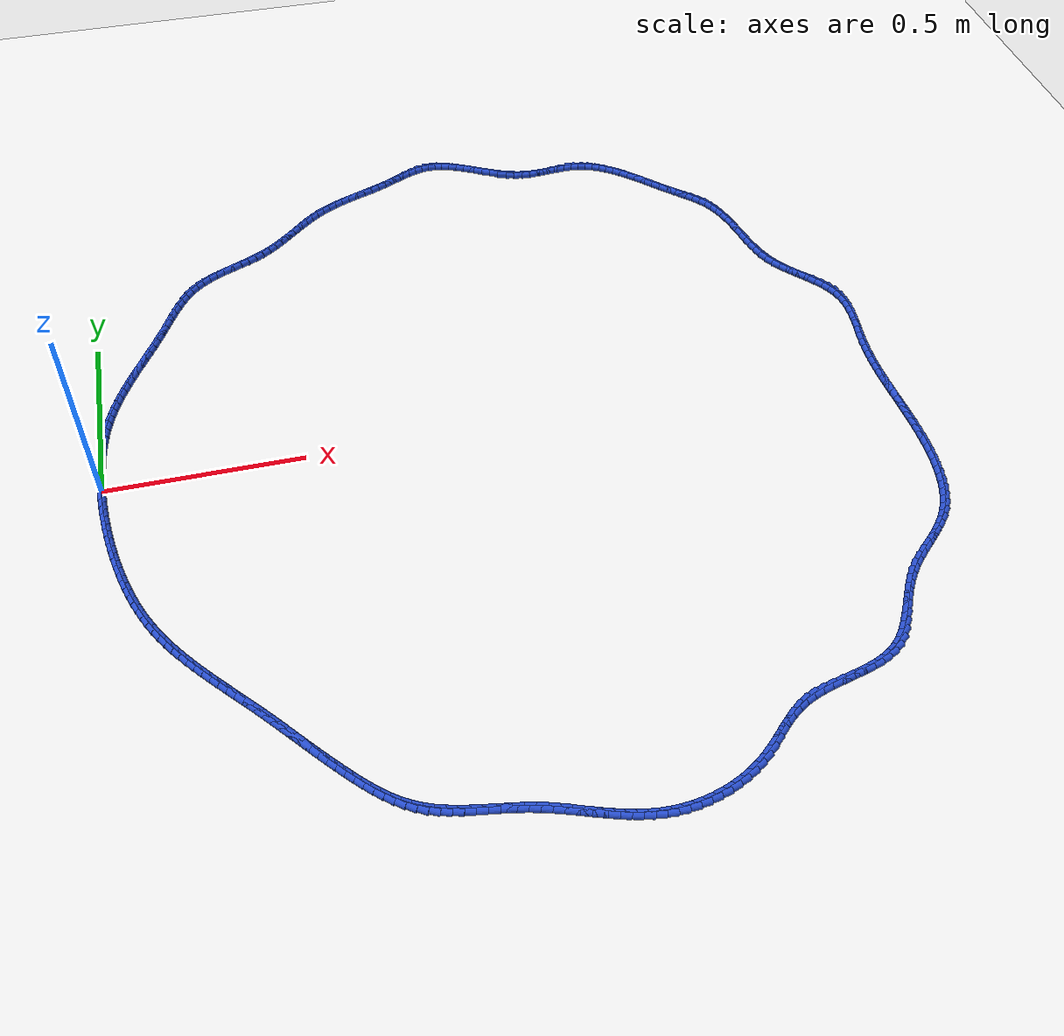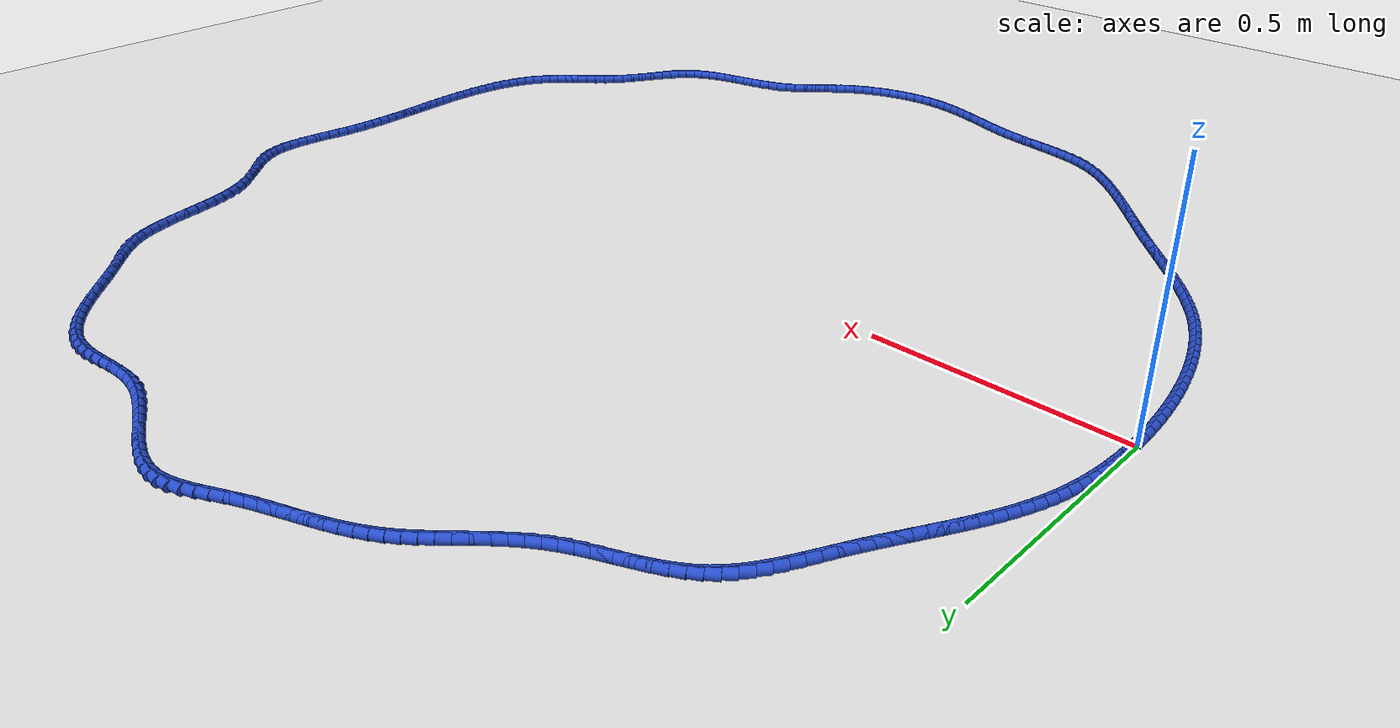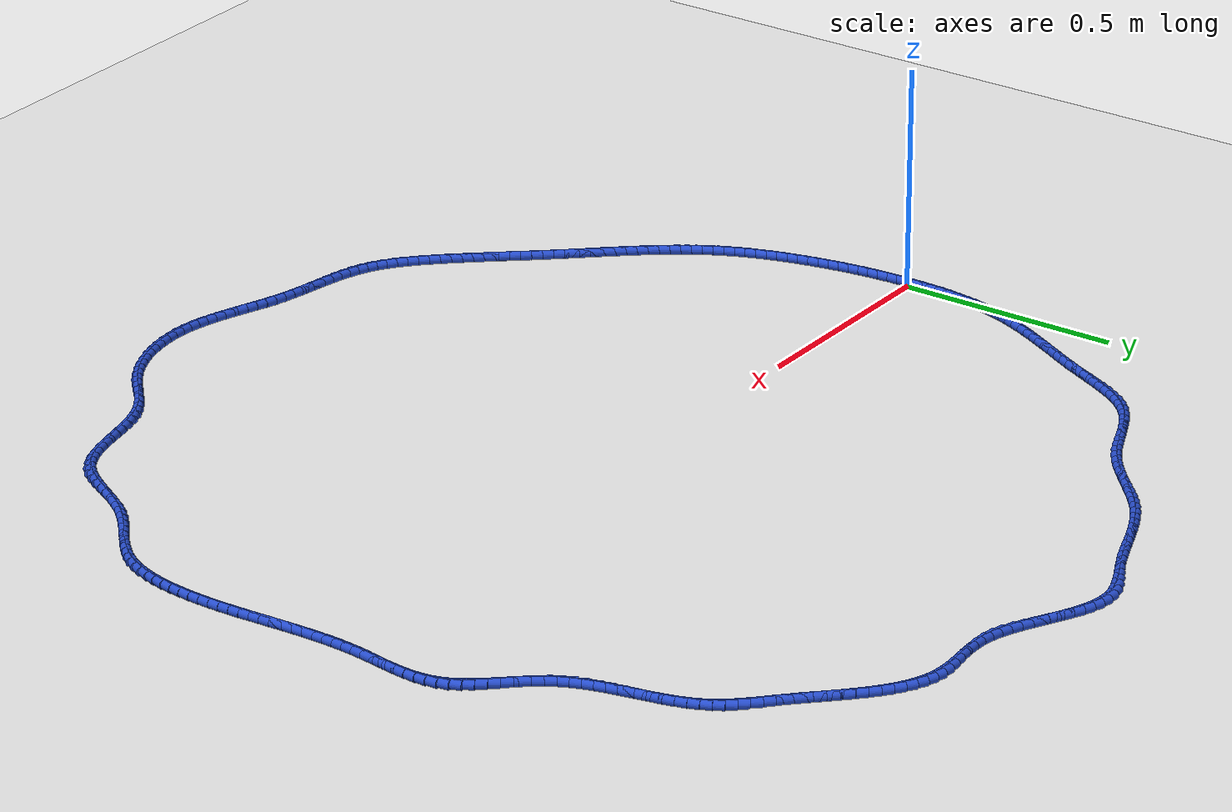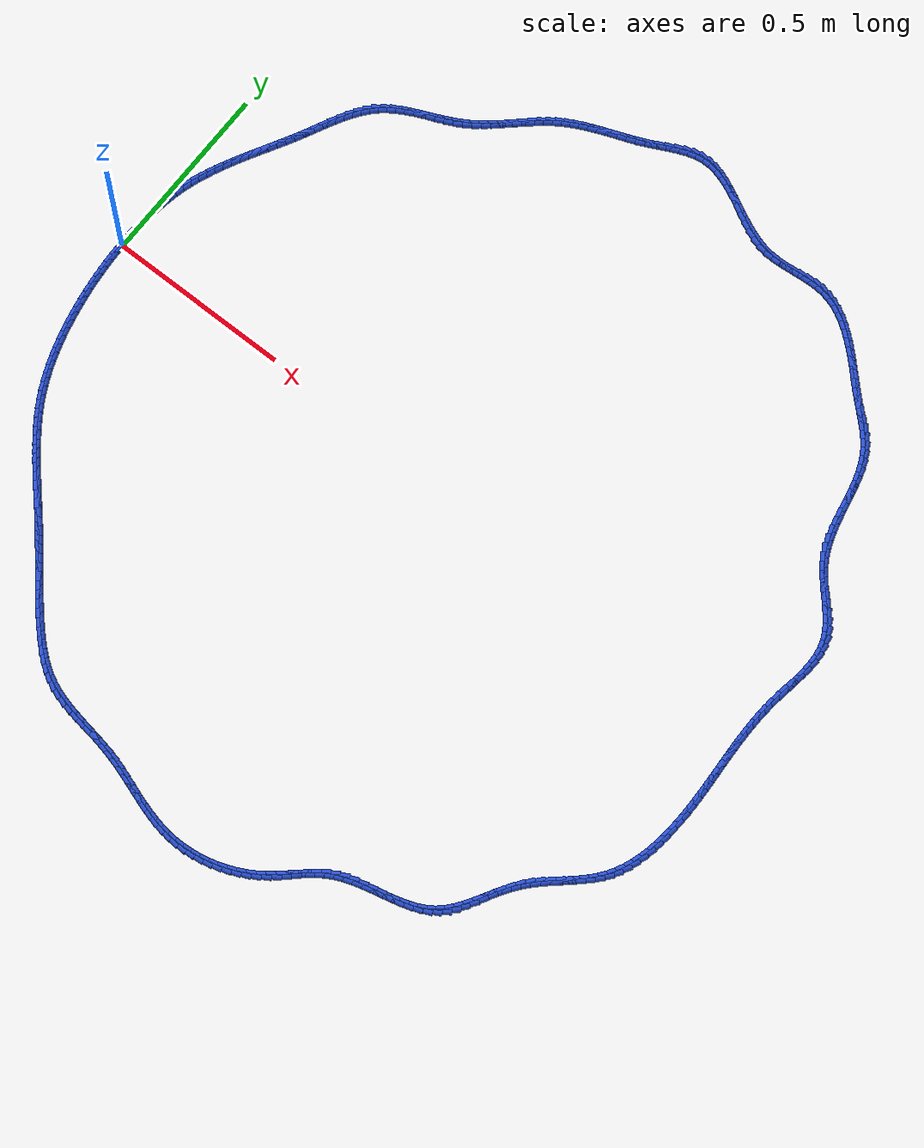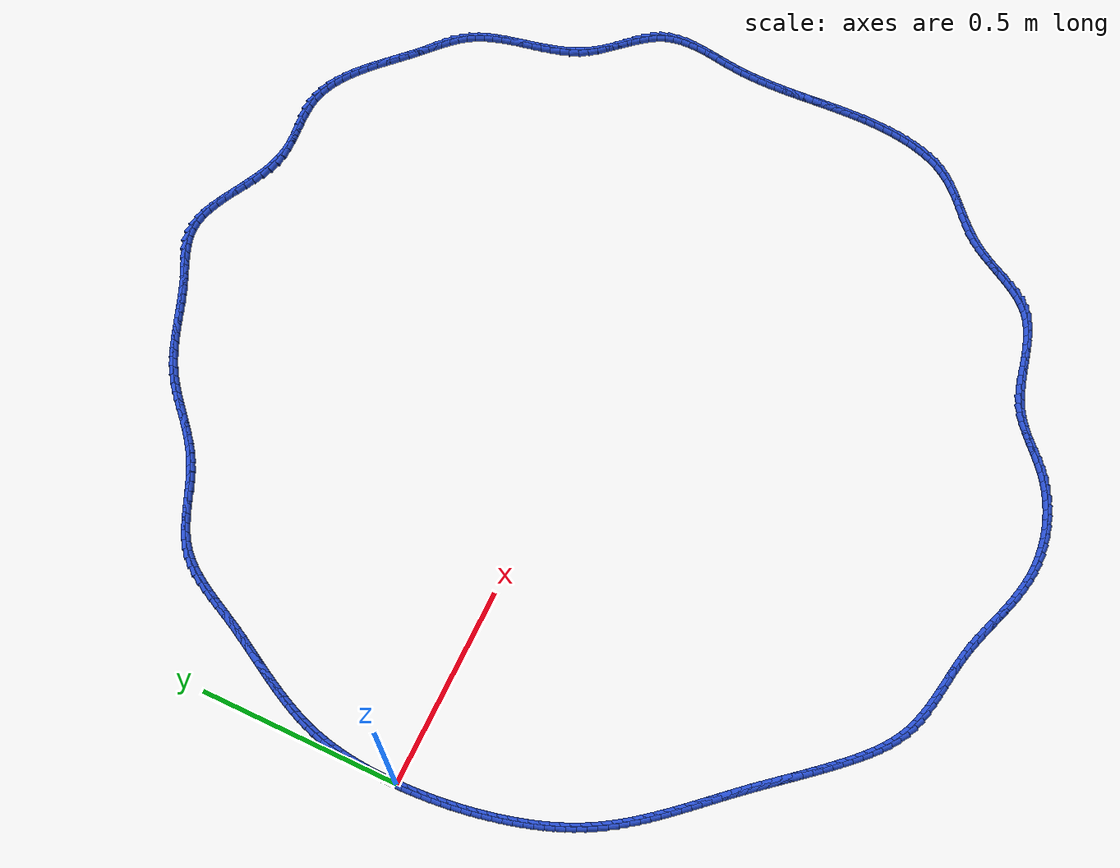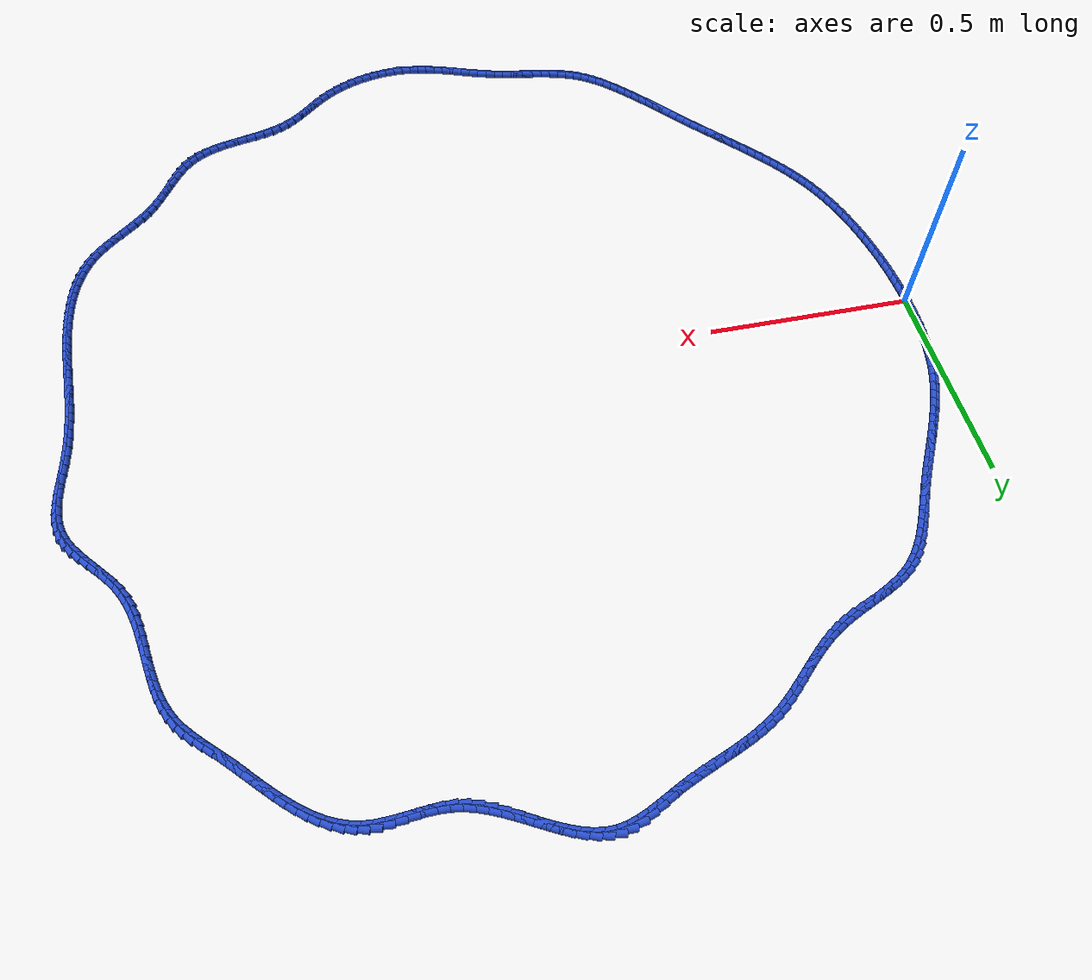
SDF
<sdf version="1.6">
 <world name="default">
  <light name="sun" type="directional">
   <pose>0 0 10 0 -0 0</pose>
   <diffuse>0.8 0.8 0.8 1</diffuse>
   <specular>0.2 0.2 0.2 1</specular>
   <attenuation>
    <range>1000</range>
    <constant>0.9</constant>
    <linear>0.01</linear>
    <quadratic>0.001</quadratic>
   </attenuation>
   <direction>-0.5 0.1 -0.9</direction>
  </light>
  <model name="ground_plane">
   <static>1</static>
   <link name="link">
    <collision name="collision">
     <geometry><plane><normal>0 0 1</normal><size>100 100</size></plane></geometry>
     <surface><friction><ode><mu>100</mu><mu2>50</mu2></ode></friction></surface>
    </collision>
    <visual name="visual">
     <cast_shadows>0</cast_shadows>
     <geometry><plane><normal>0 0 1</normal><size>100 100</size></plane></geometry>
     <material>
      <script><uri>file://media/materials/scripts/gazebo.material</uri><name>Gazebo/WhiteGlow</name></script>
     </material>
    </visual>
   </link>
  </model>
  <gravity>0 0 -9.8</gravity>
  <magnetic_field>6e-06 2.3e-05 -4.2e-05</magnetic_field>
  <atmosphere type="adiabatic"/>
  <physics name="default_physics" default="0" type="ode">
   <max_step_size>0.001</max_step_size>
   <real_time_factor>1</real_time_factor>
   <real_time_update_rate>1000</real_time_update_rate>
  </physics>
  <scene><ambient>0.4 0.4 0.4 1</ambient><background>0.7 0.7 0.7 1</background><shadows>1</shadows></scene>
  <spherical_coordinates>
   <surface_model>EARTH_WGS84</surface_model>
   <latitude_deg>0</latitude_deg>
   <longitude_deg>0</longitude_deg>
   <elevation>0</elevation>
   <heading_deg>0</heading_deg>
  </spherical_coordinates>
  <model name="line">
   <link name="link_0">
    <pose>-1.9081958235744878e-17 -1.3877787807814457e-17 0.01 0 1.57 -1.5651864543151945</pose>
    <collision name="collision">
     <geometry><cylinder><radius>0.01</radius><length>0.08</length></cylinder></geometry>
    </collision>
    <visual name="visual">
     <material>
      <script><name>Gazebo/Blue</name><uri>file://media/materials/scripts/gazebo.material</uri></script>
     </material>
     <geometry><cylinder><radius>0.01</radius><length>0.08</length></cylinder></geometry>
    </visual>
   </link>
   <link name="link_1">
    <pose>-0.00013462288452384928 0.02399724285781386 0.01 0 1.57 1.5543024262705498</pose>
    <collision name="collision">
     <geometry><cylinder><radius>0.01</radius><length>0.08</length></cylinder></geometry>
    </collision>
    <visual name="visual">
     <material>
      <script><name>Gazebo/Blue</name><uri>file://media/materials/scripts/gazebo.material</uri></script>
     </material>
     <geometry><cylinder><radius>0.01</radius><length>0.08</length></cylinder></geometry>
    </visual>
   </link>
   <link name="link_2">
    <pose>0.00026183805540674074 0.04803188441869782 0.01 0 1.57 1.5299692511264111</pose>
    <collision name="collision">
     <geometry><cylinder><radius>0.01</radius><length>0.08</length></cylinder></geometry>
    </collision>
    <visual name="visual">
     <material>
      <script><name>Gazebo/Blue</name><uri>file://media/materials/scripts/gazebo.material</uri></script>
     </material>
     <geometry><cylinder><radius>0.01</radius><length>0.08</length></cylinder></geometry>
    </visual>
   </link>
   <link name="link_3">
    <pose>0.0012430683730944615 0.07205234273181756 0.01 0 1.57 1.5032845562194308</pose>
    <collision name="collision">
     <geometry><cylinder><radius>0.01</radius><length>0.08</length></cylinder></geometry>
    </collision>
    <visual name="visual">
     <material>
      <script><name>Gazebo/Blue</name><uri>file://media/materials/scripts/gazebo.material</uri></script>
     </material>
     <geometry><cylinder><radius>0.01</radius><length>0.08</length></cylinder></geometry>
    </visual>
   </link>
   <link name="link_4">
    <pose>0.002862753621842018 0.0960070358463388 0.01 0 1.57 1.4741153371900613</pose>
    <collision name="collision">
     <geometry><cylinder><radius>0.01</radius><length>0.08</length></cylinder></geometry>
    </collision>
    <visual name="visual">
     <material>
      <script><name>Gazebo/Blue</name><uri>file://media/materials/scripts/gazebo.material</uri></script>
     </material>
     <geometry><cylinder><radius>0.01</radius><length>0.08</length></cylinder></geometry>
    </visual>
   </link>
   <link name="link_5">
    <pose>0.005174579354952117 0.11984438181142718 0.01 0 1.57 1.442320894268272</pose>
    <collision name="collision">
     <geometry><cylinder><radius>0.01</radius><length>0.08</length></cylinder></geometry>
    </collision>
    <visual name="visual">
     <material>
      <script><name>Gazebo/Blue</name><uri>file://media/materials/scripts/gazebo.material</uri></script>
     </material>
     <geometry><cylinder><radius>0.01</radius><length>0.08</length></cylinder></geometry>
    </visual>
   </link>
   <link name="link_6">
    <pose>0.008232231125727466 0.14351279867624842 0.01 0 1.57 1.4077572072235502</pose>
    <collision name="collision">
     <geometry><cylinder><radius>0.01</radius><length>0.08</length></cylinder></geometry>
    </collision>
    <visual name="visual">
     <material>
      <script><name>Gazebo/Blue</name><uri>file://media/materials/scripts/gazebo.material</uri></script>
     </material>
     <geometry><cylinder><radius>0.01</radius><length>0.08</length></cylinder></geometry>
    </visual>
   </link>
   <link name="link_7">
    <pose>0.012089394487470767 0.16696070448996814 0.01 0 1.57 1.3702828442809503</pose>
    <collision name="collision">
     <geometry><cylinder><radius>0.01</radius><length>0.08</length></cylinder></geometry>
    </collision>
    <visual name="visual">
     <material>
      <script><name>Gazebo/Blue</name><uri>file://media/materials/scripts/gazebo.material</uri></script>
     </material>
     <geometry><cylinder><radius>0.01</radius><length>0.08</length></cylinder></geometry>
    </visual>
   </link>
   <link name="link_8">
    <pose>0.01679975499348474 0.19013651730175218 0.01 0 1.57 1.3297667480762738</pose>
    <collision name="collision">
     <geometry><cylinder><radius>0.01</radius><length>0.08</length></cylinder></geometry>
    </collision>
    <visual name="visual">
     <material>
      <script><name>Gazebo/Blue</name><uri>file://media/materials/scripts/gazebo.material</uri></script>
     </material>
     <geometry><cylinder><radius>0.01</radius><length>0.08</length></cylinder></geometry>
    </visual>
   </link>
   <link name="link_9">
    <pose>0.022416998197072074 0.21298865516076604 0.01 0 1.57 1.2863288038921876</pose>
    <collision name="collision">
     <geometry><cylinder><radius>0.01</radius><length>0.08</length></cylinder></geometry>
    </collision>
    <visual name="visual">
     <material>
      <script><name>Gazebo/Blue</name><uri>file://media/materials/scripts/gazebo.material</uri></script>
     </material>
     <geometry><cylinder><radius>0.01</radius><length>0.08</length></cylinder></geometry>
    </visual>
   </link>
   <link name="link_10">
    <pose>0.028990135709450904 0.23546879697553513 0.01 0 1.57 1.243739238663926</pose>
    <collision name="collision">
     <geometry><cylinder><radius>0.01</radius><length>0.08</length></cylinder></geometry>
    </collision>
    <visual name="visual">
     <material>
      <script><name>Gazebo/Blue</name><uri>file://media/materials/scripts/gazebo.material</uri></script>
     </material>
     <geometry><cylinder><radius>0.01</radius><length>0.08</length></cylinder></geometry>
    </visual>
   </link>
   <link name="link_11">
    <pose>0.036491789879545204 0.25758191599080416 0.01 0 1.57 1.205302640160959</pose>
    <collision name="collision">
     <geometry><cylinder><radius>0.01</radius><length>0.08</length></cylinder></geometry>
    </collision>
    <visual name="visual">
     <material>
      <script><name>Gazebo/Blue</name><uri>file://media/materials/scripts/gazebo.material</uri></script>
     </material>
     <geometry><cylinder><radius>0.01</radius><length>0.08</length></cylinder></geometry>
    </visual>
   </link>
   <link name="link_12">
    <pose>0.04483229266909103 0.2793764434549473 0.01 0 1.57 1.17130982850341</pose>
    <collision name="collision">
     <geometry><cylinder><radius>0.01</radius><length>0.08</length></cylinder></geometry>
    </collision>
    <visual name="visual">
     <material>
      <script><name>Gazebo/Blue</name><uri>file://media/materials/scripts/gazebo.material</uri></script>
     </material>
     <geometry><cylinder><radius>0.01</radius><length>0.08</length></cylinder></geometry>
    </visual>
   </link>
   <link name="link_13">
    <pose>0.05392015872231206 0.30090207850043144 0.01 0 1.57 1.1418763662415876</pose>
    <collision name="collision">
     <geometry><cylinder><radius>0.01</radius><length>0.08</length></cylinder></geometry>
    </collision>
    <visual name="visual">
     <material>
      <script><name>Gazebo/Blue</name><uri>file://media/materials/scripts/gazebo.material</uri></script>
     </material>
     <geometry><cylinder><radius>0.01</radius><length>0.08</length></cylinder></geometry>
    </visual>
   </link>
   <link name="link_14">
    <pose>0.06366390268343185 0.3222085202597234 0.01 0 1.57 1.1170505330191731</pose>
    <collision name="collision">
     <geometry><cylinder><radius>0.01</radius><length>0.08</length></cylinder></geometry>
    </collision>
    <visual name="visual">
     <material>
      <script><name>Gazebo/Blue</name><uri>file://media/materials/scripts/gazebo.material</uri></script>
     </material>
     <geometry><cylinder><radius>0.01</radius><length>0.08</length></cylinder></geometry>
    </visual>
   </link>
   <link name="link_15">
    <pose>0.07397203919667412 0.3433454678652904 0.01 0 1.57 1.0968313477389688</pose>
    <collision name="collision">
     <geometry><cylinder><radius>0.01</radius><length>0.08</length></cylinder></geometry>
    </collision>
    <visual name="visual">
     <material>
      <script><name>Gazebo/Blue</name><uri>file://media/materials/scripts/gazebo.material</uri></script>
     </material>
     <geometry><cylinder><radius>0.01</radius><length>0.08</length></cylinder></geometry>
    </visual>
   </link>
   <link name="link_16">
    <pose>0.08475308290626252 0.3643626204495994 0.01 0 1.57 1.0811846470821673</pose>
    <collision name="collision">
     <geometry><cylinder><radius>0.01</radius><length>0.08</length></cylinder></geometry>
    </collision>
    <visual name="visual">
     <material>
      <script><name>Gazebo/Blue</name><uri>file://media/materials/scripts/gazebo.material</uri></script>
     </material>
     <geometry><cylinder><radius>0.01</radius><length>0.08</length></cylinder></geometry>
    </visual>
   </link>
   <link name="link_17">
    <pose>0.09591554845642061 0.385309677145117 0.01 0 1.57 1.0700563237791811</pose>
    <collision name="collision">
     <geometry><cylinder><radius>0.01</radius><length>0.08</length></cylinder></geometry>
    </collision>
    <visual name="visual">
     <material>
      <script><name>Gazebo/Blue</name><uri>file://media/materials/scripts/gazebo.material</uri></script>
     </material>
     <geometry><cylinder><radius>0.01</radius><length>0.08</length></cylinder></geometry>
    </visual>
   </link>
   <link name="link_18">
    <pose>0.1073679504913721 0.40623633708431056 0.01 0 1.57 1.0633823903744817</pose>
    <collision name="collision">
     <geometry><cylinder><radius>0.01</radius><length>0.08</length></cylinder></geometry>
    </collision>
    <visual name="visual">
     <material>
      <script><name>Gazebo/Blue</name><uri>file://media/materials/scripts/gazebo.material</uri></script>
     </material>
     <geometry><cylinder><radius>0.01</radius><length>0.08</length></cylinder></geometry>
    </visual>
   </link>
   <link name="link_19">
    <pose>0.11901880365534061 0.4271922993996468 0.01 0 1.57 1.06109588749169</pose>
    <collision name="collision">
     <geometry><cylinder><radius>0.01</radius><length>0.08</length></cylinder></geometry>
    </collision>
    <visual name="visual">
     <material>
      <script><name>Gazebo/Blue</name><uri>file://media/materials/scripts/gazebo.material</uri></script>
     </material>
     <geometry><cylinder><radius>0.01</radius><length>0.08</length></cylinder></geometry>
    </visual>
   </link>
   <link name="link_20">
    <pose>0.13077662259254974 0.44822726322359274 0.01 0 1.57 1.0631308369675894</pose>
    <collision name="collision">
     <geometry><cylinder><radius>0.01</radius><length>0.08</length></cylinder></geometry>
    </collision>
    <visual name="visual">
     <material>
      <script><name>Gazebo/Blue</name><uri>file://media/materials/scripts/gazebo.material</uri></script>
     </material>
     <geometry><cylinder><radius>0.01</radius><length>0.08</length></cylinder></geometry>
    </visual>
   </link>
   <link name="link_21">
    <pose>0.1425499219472232 0.46939092768861546 0.01 0 1.57 1.069423504282037</pose>
    <collision name="collision">
     <geometry><cylinder><radius>0.01</radius><length>0.08</length></cylinder></geometry>
    </collision>
    <visual name="visual">
     <material>
      <script><name>Gazebo/Blue</name><uri>file://media/materials/scripts/gazebo.material</uri></script>
     </material>
     <geometry><cylinder><radius>0.01</radius><length>0.08</length></cylinder></geometry>
    </visual>
   </link>
   <link name="link_22">
    <pose>0.15424721636358465 0.4907329919271818 0.01 0 1.57 1.0799112347213335</pose>
    <collision name="collision">
     <geometry><cylinder><radius>0.01</radius><length>0.08</length></cylinder></geometry>
    </collision>
    <visual name="visual">
     <material>
      <script><name>Gazebo/Blue</name><uri>file://media/materials/scripts/gazebo.material</uri></script>
     </material>
     <geometry><cylinder><radius>0.01</radius><length>0.08</length></cylinder></geometry>
    </visual>
   </link>
   <link name="link_23">
    <pose>0.16577702048585757 0.5123031550717586 0.01 0 1.57 1.0944660475812336</pose>
    <collision name="collision">
     <geometry><cylinder><radius>0.01</radius><length>0.08</length></cylinder></geometry>
    </collision>
    <visual name="visual">
     <material>
      <script><name>Gazebo/Blue</name><uri>file://media/materials/scripts/gazebo.material</uri></script>
     </material>
     <geometry><cylinder><radius>0.01</radius><length>0.08</length></cylinder></geometry>
    </visual>
   </link>
   <link name="link_24">
    <pose>0.17704902293189417 0.5341500105680198 0.01 0 1.57 1.107175532152483</pose>
    <collision name="collision">
     <geometry><cylinder><radius>0.01</radius><length>0.08</length></cylinder></geometry>
    </collision>
    <visual name="visual">
     <material>
      <script><name>Gazebo/Blue</name><uri>file://media/materials/scripts/gazebo.material</uri></script>
     </material>
     <geometry><cylinder><radius>0.01</radius><length>0.08</length></cylinder></geometry>
    </visual>
   </link>
   <link name="link_25">
    <pose>0.18808266809680688 0.556218780277762 0.01 0 1.57 1.1076003094177147</pose>
    <collision name="collision">
     <geometry><cylinder><radius>0.01</radius><length>0.08</length></cylinder></geometry>
    </collision>
    <visual name="visual">
     <material>
      <script><name>Gazebo/Blue</name><uri>file://media/materials/scripts/gazebo.material</uri></script>
     </material>
     <geometry><cylinder><radius>0.01</radius><length>0.08</length></cylinder></geometry>
    </visual>
   </link>
   <link name="link_26">
    <pose>0.19909508434511577 0.5782685008292138 0.01 0 1.57 1.0945913663082645</pose>
    <collision name="collision">
     <geometry><cylinder><radius>0.01</radius><length>0.08</length></cylinder></geometry>
    </collision>
    <visual name="visual">
     <material>
      <script><name>Gazebo/Blue</name><uri>file://media/materials/scripts/gazebo.material</uri></script>
     </material>
     <geometry><cylinder><radius>0.01</radius><length>0.08</length></cylinder></geometry>
    </visual>
   </link>
   <link name="link_27">
    <pose>0.21032409189719106 0.6000387205834156 0.01 0 1.57 1.067708249834815</pose>
    <collision name="collision">
     <geometry><cylinder><radius>0.01</radius><length>0.08</length></cylinder></geometry>
    </collision>
    <visual name="visual">
     <material>
      <script><name>Gazebo/Blue</name><uri>file://media/materials/scripts/gazebo.material</uri></script>
     </material>
     <geometry><cylinder><radius>0.01</radius><length>0.08</length></cylinder></geometry>
    </visual>
   </link>
   <link name="link_28">
    <pose>0.22200751097340343 0.6212689879014088 0.01 0 1.57 1.0261502567329615</pose>
    <collision name="collision">
     <geometry><cylinder><radius>0.01</radius><length>0.08</length></cylinder></geometry>
    </collision>
    <visual name="visual">
     <material>
      <script><name>Gazebo/Blue</name><uri>file://media/materials/scripts/gazebo.material</uri></script>
     </material>
     <geometry><cylinder><radius>0.01</radius><length>0.08</length></cylinder></geometry>
    </visual>
   </link>
   <link name="link_29">
    <pose>0.23438316179412327 0.6416988511442344 0.01 0 1.57 0.9688768317061921</pose>
    <collision name="collision">
     <geometry><cylinder><radius>0.01</radius><length>0.08</length></cylinder></geometry>
    </collision>
    <visual name="visual">
     <material>
      <script><name>Gazebo/Blue</name><uri>file://media/materials/scripts/gazebo.material</uri></script>
     </material>
     <geometry><cylinder><radius>0.01</radius><length>0.08</length></cylinder></geometry>
    </visual>
   </link>
   <link name="link_30">
    <pose>0.247688864579721 0.661067858672933 0.01 0 1.57 0.89486001078155</pose>
    <collision name="collision">
     <geometry><cylinder><radius>0.01</radius><length>0.08</length></cylinder></geometry>
    </collision>
    <visual name="visual">
     <material>
      <script><name>Gazebo/Blue</name><uri>file://media/materials/scripts/gazebo.material</uri></script>
     </material>
     <geometry><cylinder><radius>0.01</radius><length>0.08</length></cylinder></geometry>
    </visual>
   </link>
   <link name="link_31">
    <pose>0.26216243955056695 0.6791155588485454 0.01 0 1.57 0.8035340639117122</pose>
    <collision name="collision">
     <geometry><cylinder><radius>0.01</radius><length>0.08</length></cylinder></geometry>
    </collision>
    <visual name="visual">
     <material>
      <script><name>Gazebo/Blue</name><uri>file://media/materials/scripts/gazebo.material</uri></script>
     </material>
     <geometry><cylinder><radius>0.01</radius><length>0.08</length></cylinder></geometry>
    </visual>
   </link>
   <link name="link_32">
    <pose>0.27804170692703173 0.6955815000321126 0.01 0 1.57 0.6976796595252164</pose>
    <collision name="collision">
     <geometry><cylinder><radius>0.01</radius><length>0.08</length></cylinder></geometry>
    </collision>
    <visual name="visual">
     <material>
      <script><name>Gazebo/Blue</name><uri>file://media/materials/scripts/gazebo.material</uri></script>
     </material>
     <geometry><cylinder><radius>0.01</radius><length>0.08</length></cylinder></geometry>
    </visual>
   </link>
   <link name="link_33">
    <pose>0.295531459427038 0.7102436773371184 0.01 0 1.57 0.6003637925885659</pose>
    <collision name="collision">
     <geometry><cylinder><radius>0.01</radius><length>0.08</length></cylinder></geometry>
    </collision>
    <visual name="visual">
     <material>
      <script><name>Gazebo/Blue</name><uri>file://media/materials/scripts/gazebo.material</uri></script>
     </material>
     <geometry><cylinder><radius>0.01</radius><length>0.08</length></cylinder></geometry>
    </visual>
   </link>
   <link name="link_34">
    <pose>0.314522123448611 0.7232460343497255 0.01 0 1.57 0.5244140772334347</pose>
    <collision name="collision">
     <geometry><cylinder><radius>0.01</radius><length>0.08</length></cylinder></geometry>
    </collision>
    <visual name="visual">
     <material>
      <script><name>Gazebo/Blue</name><uri>file://media/materials/scripts/gazebo.material</uri></script>
     </material>
     <geometry><cylinder><radius>0.01</radius><length>0.08</length></cylinder></geometry>
    </visual>
   </link>
   <link name="link_35">
    <pose>0.3347301010224503 0.7349350934547854 0.01 0 1.57 0.4694774644040979</pose>
    <collision name="collision">
     <geometry><cylinder><radius>0.01</radius><length>0.08</length></cylinder></geometry>
    </collision>
    <visual name="visual">
     <material>
      <script><name>Gazebo/Blue</name><uri>file://media/materials/scripts/gazebo.material</uri></script>
     </material>
     <geometry><cylinder><radius>0.01</radius><length>0.08</length></cylinder></geometry>
    </visual>
   </link>
   <link name="link_36">
    <pose>0.35586995055137965 0.7456595231729224 0.01 0 1.57 0.43442135593654135</pose>
    <collision name="collision">
     <geometry><cylinder><radius>0.01</radius><length>0.08</length></cylinder></geometry>
    </collision>
    <visual name="visual">
     <material>
      <script><name>Gazebo/Blue</name><uri>file://media/materials/scripts/gazebo.material</uri></script>
     </material>
     <geometry><cylinder><radius>0.01</radius><length>0.08</length></cylinder></geometry>
    </visual>
   </link>
   <link name="link_37">
    <pose>0.37765623043822316 0.7557679920247604 0.01 0 1.57 0.41814688173799847</pose>
    <collision name="collision">
     <geometry><cylinder><radius>0.01</radius><length>0.08</length></cylinder></geometry>
    </collision>
    <visual name="visual">
     <material>
      <script><name>Gazebo/Blue</name><uri>file://media/materials/scripts/gazebo.material</uri></script>
     </material>
     <geometry><cylinder><radius>0.01</radius><length>0.08</length></cylinder></geometry>
    </visual>
   </link>
   <link name="link_38">
    <pose>0.39980349908580454 0.7656091685309241 0.01 0 1.57 0.41994196879016</pose>
    <collision name="collision">
     <geometry><cylinder><radius>0.01</radius><length>0.08</length></cylinder></geometry>
    </collision>
    <visual name="visual">
     <material>
      <script><name>Gazebo/Blue</name><uri>file://media/materials/scripts/gazebo.material</uri></script>
     </material>
     <geometry><cylinder><radius>0.01</radius><length>0.08</length></cylinder></geometry>
    </visual>
   </link>
   <link name="link_39">
    <pose>0.4220263148969479 0.7755317212120377 0.01 0 1.57 0.4396036201237757</pose>
    <collision name="collision">
     <geometry><cylinder><radius>0.01</radius><length>0.08</length></cylinder></geometry>
    </collision>
    <visual name="visual">
     <material>
      <script><name>Gazebo/Blue</name><uri>file://media/materials/scripts/gazebo.material</uri></script>
     </material>
     <geometry><cylinder><radius>0.01</radius><length>0.08</length></cylinder></geometry>
    </visual>
   </link>
   <link name="link_40">
    <pose>0.4440392362744769 0.7858843185887256 0.01 0 1.57 0.47740129657258207</pose>
    <collision name="collision">
     <geometry><cylinder><radius>0.01</radius><length>0.08</length></cylinder></geometry>
    </collision>
    <visual name="visual">
     <material>
      <script><name>Gazebo/Blue</name><uri>file://media/materials/scripts/gazebo.material</uri></script>
     </material>
     <geometry><cylinder><radius>0.01</radius><length>0.08</length></cylinder></geometry>
    </visual>
   </link>
   <link name="link_41">
    <pose>0.46555682162121576 0.7970156291816124 0.01 0 1.57 0.5338497902758922</pose>
    <collision name="collision">
     <geometry><cylinder><radius>0.01</radius><length>0.08</length></cylinder></geometry>
    </collision>
    <visual name="visual">
     <material>
      <script><name>Gazebo/Blue</name><uri>file://media/materials/scripts/gazebo.material</uri></script>
     </material>
     <geometry><cylinder><radius>0.01</radius><length>0.08</length></cylinder></geometry>
    </visual>
   </link>
   <link name="link_42">
    <pose>0.4862942278078413 0.8092735130483321 0.01 0 1.57 0.6002563167692372</pose>
    <collision name="collision">
     <geometry><cylinder><radius>0.01</radius><length>0.08</length></cylinder></geometry>
    </collision>
    <visual name="visual">
     <material>
      <script><name>Gazebo/Blue</name><uri>file://media/materials/scripts/gazebo.material</uri></script>
     </material>
     <geometry><cylinder><radius>0.01</radius><length>0.08</length></cylinder></geometry>
    </visual>
   </link>
   <link name="link_43">
    <pose>0.5060974515509926 0.8228290802798162 0.01 0 1.57 0.6558638564405528</pose>
    <collision name="collision">
     <geometry><cylinder><radius>0.01</radius><length>0.08</length></cylinder></geometry>
    </collision>
    <visual name="visual">
     <material>
      <script><name>Gazebo/Blue</name><uri>file://media/materials/scripts/gazebo.material</uri></script>
     </material>
     <geometry><cylinder><radius>0.01</radius><length>0.08</length></cylinder></geometry>
    </visual>
   </link>
   <link name="link_44">
    <pose>0.5251063819955805 0.8374564252373553 0.01 0 1.57 0.6976268493920837</pose>
    <collision name="collision">
     <geometry><cylinder><radius>0.01</radius><length>0.08</length></cylinder></geometry>
    </collision>
    <visual name="visual">
     <material>
      <script><name>Gazebo/Blue</name><uri>file://media/materials/scripts/gazebo.material</uri></script>
     </material>
     <geometry><cylinder><radius>0.01</radius><length>0.08</length></cylinder></geometry>
    </visual>
   </link>
   <link name="link_45">
    <pose>0.5435009812020578 0.8528755082649151 0.01 0 1.57 0.7255879669118305</pose>
    <collision name="collision">
     <geometry><cylinder><radius>0.01</radius><length>0.08</length></cylinder></geometry>
    </collision>
    <visual name="visual">
     <material>
      <script><name>Gazebo/Blue</name><uri>file://media/materials/scripts/gazebo.material</uri></script>
     </material>
     <geometry><cylinder><radius>0.01</radius><length>0.08</length></cylinder></geometry>
    </visual>
   </link>
   <link name="link_46">
    <pose>0.5614612112308782 0.868806289706463 0.01 0 1.57 0.7398594924105822</pose>
    <collision name="collision">
     <geometry><cylinder><radius>0.01</radius><length>0.08</length></cylinder></geometry>
    </collision>
    <visual name="visual">
     <material>
      <script><name>Gazebo/Blue</name><uri>file://media/materials/scripts/gazebo.material</uri></script>
     </material>
     <geometry><cylinder><radius>0.01</radius><length>0.08</length></cylinder></geometry>
    </visual>
   </link>
   <link name="link_47">
    <pose>0.579167034142495 0.8849687299059654 0.01 0 1.57 0.7404647625278731</pose>
    <collision name="collision">
     <geometry><cylinder><radius>0.01</radius><length>0.08</length></cylinder></geometry>
    </collision>
    <visual name="visual">
     <material>
      <script><name>Gazebo/Blue</name><uri>file://media/materials/scripts/gazebo.material</uri></script>
     </material>
     <geometry><cylinder><radius>0.01</radius><length>0.08</length></cylinder></geometry>
    </visual>
   </link>
   <link name="link_48">
    <pose>0.5967984119973614 0.9010827892073897 0.01 0 1.57 0.7272564690289197</pose>
    <collision name="collision">
     <geometry><cylinder><radius>0.01</radius><length>0.08</length></cylinder></geometry>
    </collision>
    <visual name="visual">
     <material>
      <script><name>Gazebo/Blue</name><uri>file://media/materials/scripts/gazebo.material</uri></script>
     </material>
     <geometry><cylinder><radius>0.01</radius><length>0.08</length></cylinder></geometry>
    </visual>
   </link>
   <link name="link_49">
    <pose>0.6145353068559303 0.9168684279547016 0.01 0 1.57 0.6999072384496045</pose>
    <collision name="collision">
     <geometry><cylinder><radius>0.01</radius><length>0.08</length></cylinder></geometry>
    </collision>
    <visual name="visual">
     <material>
      <script><name>Gazebo/Blue</name><uri>file://media/materials/scripts/gazebo.material</uri></script>
     </material>
     <geometry><cylinder><radius>0.01</radius><length>0.08</length></cylinder></geometry>
    </visual>
   </link>
   <link name="link_50">
    <pose>0.6325576807786556 0.9320456064918688 0.01 0 1.57 0.6579780008543169</pose>
    <collision name="collision">
     <geometry><cylinder><radius>0.01</radius><length>0.08</length></cylinder></geometry>
    </collision>
    <visual name="visual">
     <material>
      <script><name>Gazebo/Blue</name><uri>file://media/materials/scripts/gazebo.material</uri></script>
     </material>
     <geometry><cylinder><radius>0.01</radius><length>0.08</length></cylinder></geometry>
    </visual>
   </link>
   <link name="link_51">
    <pose>0.65104549582599 0.9463342851628574 0.01 0 1.57 0.601204826072576</pose>
    <collision name="collision">
     <geometry><cylinder><radius>0.01</radius><length>0.08</length></cylinder></geometry>
    </collision>
    <visual name="visual">
     <material>
      <script><name>Gazebo/Blue</name><uri>file://media/materials/scripts/gazebo.material</uri></script>
     </material>
     <geometry><cylinder><radius>0.01</radius><length>0.08</length></cylinder></geometry>
    </visual>
   </link>
   <link name="link_52">
    <pose>0.6701773530000044 0.9594569600171895 0.01 0 1.57 0.5382422064544571</pose>
    <collision name="collision">
     <geometry><cylinder><radius>0.01</radius><length>0.08</length></cylinder></geometry>
    </collision>
    <visual name="visual">
     <material>
      <script><name>Gazebo/Blue</name><uri>file://media/materials/scripts/gazebo.material</uri></script>
     </material>
     <geometry><cylinder><radius>0.01</radius><length>0.08</length></cylinder></geometry>
    </visual>
   </link>
   <link name="link_53">
    <pose>0.6900365221695057 0.9713137327730604 0.01 0 1.57 0.4839202281921699</pose>
    <collision name="collision">
     <geometry><cylinder><radius>0.01</radius><length>0.08</length></cylinder></geometry>
    </collision>
    <visual name="visual">
     <material>
      <script><name>Gazebo/Blue</name><uri>file://media/materials/scripts/gazebo.material</uri></script>
     </material>
     <geometry><cylinder><radius>0.01</radius><length>0.08</length></cylinder></geometry>
    </visual>
   </link>
   <link name="link_54">
    <pose>0.7105500642330171 0.982095728633549 0.01 0 1.57 0.4400397293444088</pose>
    <collision name="collision">
     <geometry><cylinder><radius>0.01</radius><length>0.08</length></cylinder></geometry>
    </collision>
    <visual name="visual">
     <material>
      <script><name>Gazebo/Blue</name><uri>file://media/materials/scripts/gazebo.material</uri></script>
     </material>
     <geometry><cylinder><radius>0.01</radius><length>0.08</length></cylinder></geometry>
    </visual>
   </link>
   <link name="link_55">
    <pose>0.7316305647468763 0.9920210409362787 0.01 0 1.57 0.4067204012210863</pose>
    <collision name="collision">
     <geometry><cylinder><radius>0.01</radius><length>0.08</length></cylinder></geometry>
    </collision>
    <visual name="visual">
     <material>
      <script><name>Gazebo/Blue</name><uri>file://media/materials/scripts/gazebo.material</uri></script>
     </material>
     <geometry><cylinder><radius>0.01</radius><length>0.08</length></cylinder></geometry>
    </visual>
   </link>
   <link name="link_56">
    <pose>0.75319060926742 1.001307763018873 0.01 0 1.57 0.3838538170917643</pose>
    <collision name="collision">
     <geometry><cylinder><radius>0.01</radius><length>0.08</length></cylinder></geometry>
    </collision>
    <visual name="visual">
     <material>
      <script><name>Gazebo/Blue</name><uri>file://media/materials/scripts/gazebo.material</uri></script>
     </material>
     <geometry><cylinder><radius>0.01</radius><length>0.08</length></cylinder></geometry>
    </visual>
   </link>
   <link name="link_57">
    <pose>0.7751427833509863 1.0101739882189553 0.01 0 1.57 0.3712177031046744</pose>
    <collision name="collision">
     <geometry><cylinder><radius>0.01</radius><length>0.08</length></cylinder></geometry>
    </collision>
    <visual name="visual">
     <material>
      <script><name>Gazebo/Blue</name><uri>file://media/materials/scripts/gazebo.material</uri></script>
     </material>
     <geometry><cylinder><radius>0.01</radius><length>0.08</length></cylinder></geometry>
    </visual>
   </link>
   <link name="link_58">
    <pose>0.7973996725539123 1.0188378098741486 0.01 0 1.57 0.36855271194304695</pose>
    <collision name="collision">
     <geometry><cylinder><radius>0.01</radius><length>0.08</length></cylinder></geometry>
    </collision>
    <visual name="visual">
     <material>
      <script><name>Gazebo/Blue</name><uri>file://media/materials/scripts/gazebo.material</uri></script>
     </material>
     <geometry><cylinder><radius>0.01</radius><length>0.08</length></cylinder></geometry>
    </visual>
   </link>
   <link name="link_59">
    <pose>0.8198738624325361 1.0275173213220772 0.01 0 1.57 0.3756023721718916</pose>
    <collision name="collision">
     <geometry><cylinder><radius>0.01</radius><length>0.08</length></cylinder></geometry>
    </collision>
    <visual name="visual">
     <material>
      <script><name>Gazebo/Blue</name><uri>file://media/materials/scripts/gazebo.material</uri></script>
     </material>
     <geometry><cylinder><radius>0.01</radius><length>0.08</length></cylinder></geometry>
    </visual>
   </link>
   <link name="link_60">
    <pose>0.8424779385431943 1.0364306159003638 0.01 0 1.57 0.3921209172730679</pose>
    <collision name="collision">
     <geometry><cylinder><radius>0.01</radius><length>0.08</length></cylinder></geometry>
    </collision>
    <visual name="visual">
     <material>
      <script><name>Gazebo/Blue</name><uri>file://media/materials/scripts/gazebo.material</uri></script>
     </material>
     <geometry><cylinder><radius>0.01</radius><length>0.08</length></cylinder></geometry>
    </visual>
   </link>
   <link name="link_61">
    <pose>0.8651244864422253 1.0457957869466317 0.01 0 1.57 0.4178541737620026</pose>
    <collision name="collision">
     <geometry><cylinder><radius>0.01</radius><length>0.08</length></cylinder></geometry>
    </collision>
    <visual name="visual">
     <material>
      <script><name>Gazebo/Blue</name><uri>file://media/materials/scripts/gazebo.material</uri></script>
     </material>
     <geometry><cylinder><radius>0.01</radius><length>0.08</length></cylinder></geometry>
    </visual>
   </link>
   <link name="link_62">
    <pose>0.8877260916859657 1.0558309277985045 0.01 0 1.57 0.44629120481709333</pose>
    <collision name="collision">
     <geometry><cylinder><radius>0.01</radius><length>0.08</length></cylinder></geometry>
    </collision>
    <visual name="visual">
     <material>
      <script><name>Gazebo/Blue</name><uri>file://media/materials/scripts/gazebo.material</uri></script>
     </material>
     <geometry><cylinder><radius>0.01</radius><length>0.08</length></cylinder></geometry>
    </visual>
   </link>
   <link name="link_63">
    <pose>0.9102110729810605 1.0665897442699426 0.01 0 1.57 0.45213760038423545</pose>
    <collision name="collision">
     <geometry><cylinder><radius>0.01</radius><length>0.08</length></cylinder></geometry>
    </collision>
    <visual name="visual">
     <material>
      <script><name>Gazebo/Blue</name><uri>file://media/materials/scripts/gazebo.material</uri></script>
     </material>
     <geometry><cylinder><radius>0.01</radius><length>0.08</length></cylinder></geometry>
    </visual>
   </link>
   <link name="link_64">
    <pose>0.9325723933193313 1.0774505075828478 0.01 0 1.57 0.42868030031112375</pose>
    <collision name="collision">
     <geometry><cylinder><radius>0.01</radius><length>0.08</length></cylinder></geometry>
    </collision>
    <visual name="visual">
     <material>
      <script><name>Gazebo/Blue</name><uri>file://media/materials/scripts/gazebo.material</uri></script>
     </material>
     <geometry><cylinder><radius>0.01</radius><length>0.08</length></cylinder></geometry>
    </visual>
   </link>
   <link name="link_65">
    <pose>0.9548196162597582 1.08761803824687 0.01 0 1.57 0.37355892491789977</pose>
    <collision name="collision">
     <geometry><cylinder><radius>0.01</radius><length>0.08</length></cylinder></geometry>
    </collision>
    <visual name="visual">
     <material>
      <script><name>Gazebo/Blue</name><uri>file://media/materials/scripts/gazebo.material</uri></script>
     </material>
     <geometry><cylinder><radius>0.01</radius><length>0.08</length></cylinder></geometry>
    </visual>
   </link>
   <link name="link_66">
    <pose>0.9769623053728899 1.096297156650803 0.01 0 1.57 0.28232804513062404</pose>
    <collision name="collision">
     <geometry><cylinder><radius>0.01</radius><length>0.08</length></cylinder></geometry>
    </collision>
    <visual name="visual">
     <material>
      <script><name>Gazebo/Blue</name><uri>file://media/materials/scripts/gazebo.material</uri></script>
     </material>
     <geometry><cylinder><radius>0.01</radius><length>0.08</length></cylinder></geometry>
    </visual>
   </link>
   <link name="link_67">
    <pose>0.9990100242292734 1.102692683183439 0.01 0 1.57 0.1498938440151525</pose>
    <collision name="collision">
     <geometry><cylinder><radius>0.01</radius><length>0.08</length></cylinder></geometry>
    </collision>
    <visual name="visual">
     <material>
      <script><name>Gazebo/Blue</name><uri>file://media/materials/scripts/gazebo.material</uri></script>
     </material>
     <geometry><cylinder><radius>0.01</radius><length>0.08</length></cylinder></geometry>
    </visual>
   </link>
   <link name="link_68">
    <pose>1.0209723391560148 1.1060095777918257 0.01 0 1.57 -0.01249065189166827</pose>
    <collision name="collision">
     <geometry><cylinder><radius>0.01</radius><length>0.08</length></cylinder></geometry>
    </collision>
    <visual name="visual">
     <material>
      <script><name>Gazebo/Blue</name><uri>file://media/materials/scripts/gazebo.material</uri></script>
     </material>
     <geometry><cylinder><radius>0.01</radius><length>0.08</length></cylinder></geometry>
    </visual>
   </link>
   <link name="link_69">
    <pose>1.042864412561768 1.1057361173021407 0.01 0 1.57 -0.15869506629257948</pose>
    <collision name="collision">
     <geometry><cylinder><radius>0.01</radius><length>0.08</length></cylinder></geometry>
    </collision>
    <visual name="visual">
     <material>
      <script><name>Gazebo/Blue</name><uri>file://media/materials/scripts/gazebo.material</uri></script>
     </material>
     <geometry><cylinder><radius>0.01</radius><length>0.08</length></cylinder></geometry>
    </visual>
   </link>
   <link name="link_70">
    <pose>1.064718748201017 1.1022385314326395 0.01 0 1.57 -0.27585993331334396</pose>
    <collision name="collision">
     <geometry><cylinder><radius>0.01</radius><length>0.08</length></cylinder></geometry>
    </collision>
    <visual name="visual">
     <material>
      <script><name>Gazebo/Blue</name><uri>file://media/materials/scripts/gazebo.material</uri></script>
     </material>
     <geometry><cylinder><radius>0.01</radius><length>0.08</length></cylinder></geometry>
    </visual>
   </link>
   <link name="link_71">
    <pose>1.0865711987899338 1.0960526002139346 0.01 0 1.57 -0.3640114104458545</pose>
    <collision name="collision">
     <geometry><cylinder><radius>0.01</radius><length>0.08</length></cylinder></geometry>
    </collision>
    <visual name="visual">
     <material>
      <script><name>Gazebo/Blue</name><uri>file://media/materials/scripts/gazebo.material</uri></script>
     </material>
     <geometry><cylinder><radius>0.01</radius><length>0.08</length></cylinder></geometry>
    </visual>
   </link>
   <link name="link_72">
    <pose>1.1084576170446931 1.0877141036766385 0.01 0 1.57 -0.4256899796307598</pose>
    <collision name="collision">
     <geometry><cylinder><radius>0.01</radius><length>0.08</length></cylinder></geometry>
    </collision>
    <visual name="visual">
     <material>
      <script><name>Gazebo/Blue</name><uri>file://media/materials/scripts/gazebo.material</uri></script>
     </material>
     <geometry><cylinder><radius>0.01</radius><length>0.08</length></cylinder></geometry>
    </visual>
   </link>
   <link name="link_73">
    <pose>1.1304138556814687 1.077758821851364 0.01 0 1.57 -0.4638409086529712</pose>
    <collision name="collision">
     <geometry><cylinder><radius>0.01</radius><length>0.08</length></cylinder></geometry>
    </collision>
    <visual name="visual">
     <material>
      <script><name>Gazebo/Blue</name><uri>file://media/materials/scripts/gazebo.material</uri></script>
     </material>
     <geometry><cylinder><radius>0.01</radius><length>0.08</length></cylinder></geometry>
    </visual>
   </link>
   <link name="link_74">
    <pose>1.1524757674164334 1.0667225347687237 0.01 0 1.57 -0.48078496858470426</pose>
    <collision name="collision">
     <geometry><cylinder><radius>0.01</radius><length>0.08</length></cylinder></geometry>
    </collision>
    <visual name="visual">
     <material>
      <script><name>Gazebo/Blue</name><uri>file://media/materials/scripts/gazebo.material</uri></script>
     </material>
     <geometry><cylinder><radius>0.01</radius><length>0.08</length></cylinder></geometry>
    </visual>
   </link>
   <link name="link_75">
    <pose>1.1746792049657615 1.05514102245933 0.01 0 1.57 -0.47786248320344155</pose>
    <collision name="collision">
     <geometry><cylinder><radius>0.01</radius><length>0.08</length></cylinder></geometry>
    </collision>
    <visual name="visual">
     <material>
      <script><name>Gazebo/Blue</name><uri>file://media/materials/scripts/gazebo.material</uri></script>
     </material>
     <geometry><cylinder><radius>0.01</radius><length>0.08</length></cylinder></geometry>
    </visual>
   </link>
   <link name="link_76">
    <pose>1.197060021045627 1.0435500649537963 0.01 0 1.57 -0.4553850498003765</pose>
    <collision name="collision">
     <geometry><cylinder><radius>0.01</radius><length>0.08</length></cylinder></geometry>
    </collision>
    <visual name="visual">
     <material>
      <script><name>Gazebo/Blue</name><uri>file://media/materials/scripts/gazebo.material</uri></script>
     </material>
     <geometry><cylinder><radius>0.01</radius><length>0.08</length></cylinder></geometry>
    </visual>
   </link>
   <link name="link_77">
    <pose>1.2196540683722024 1.0324854422827339 0.01 0 1.57 -0.4127277858807779</pose>
    <collision name="collision">
     <geometry><cylinder><radius>0.01</radius><length>0.08</length></cylinder></geometry>
    </collision>
    <visual name="visual">
     <material>
      <script><name>Gazebo/Blue</name><uri>file://media/materials/scripts/gazebo.material</uri></script>
     </material>
     <geometry><cylinder><radius>0.01</radius><length>0.08</length></cylinder></geometry>
    </visual>
   </link>
   <link name="link_78">
    <pose>1.242497199661663 1.0224829344767565 0.01 0 1.57 -0.34855737841169315</pose>
    <collision name="collision">
     <geometry><cylinder><radius>0.01</radius><length>0.08</length></cylinder></geometry>
    </collision>
    <visual name="visual">
     <material>
      <script><name>Gazebo/Blue</name><uri>file://media/materials/scripts/gazebo.material</uri></script>
     </material>
     <geometry><cylinder><radius>0.01</radius><length>0.08</length></cylinder></geometry>
    </visual>
   </link>
   <link name="link_79">
    <pose>1.265625267630181 1.0140783215664761 0.01 0 1.57 -0.2613153121712527</pose>
    <collision name="collision">
     <geometry><cylinder><radius>0.01</radius><length>0.08</length></cylinder></geometry>
    </collision>
    <visual name="visual">
     <material>
      <script><name>Gazebo/Blue</name><uri>file://media/materials/scripts/gazebo.material</uri></script>
     </material>
     <geometry><cylinder><radius>0.01</radius><length>0.08</length></cylinder></geometry>
    </visual>
   </link>
   <link name="link_80">
    <pose>1.2890741249939304 1.0078073835825059 0.01 0 1.57 -0.15103770888624535</pose>
    <collision name="collision">
     <geometry><cylinder><radius>0.01</radius><length>0.08</length></cylinder></geometry>
    </collision>
    <visual name="visual">
     <material>
      <script><name>Gazebo/Blue</name><uri>file://media/materials/scripts/gazebo.material</uri></script>
     </material>
     <geometry><cylinder><radius>0.01</radius><length>0.08</length></cylinder></geometry>
    </visual>
   </link>
   <link name="link_81">
    <pose>1.3128765174459731 1.0041847356900666 0.01 0 1.57 -0.043911674486950776</pose>
    <collision name="collision">
     <geometry><cylinder><radius>0.01</radius><length>0.08</length></cylinder></geometry>
    </collision>
    <visual name="visual">
     <material>
      <script><name>Gazebo/Blue</name><uri>file://media/materials/scripts/gazebo.material</uri></script>
     </material>
     <geometry><cylinder><radius>0.01</radius><length>0.08</length></cylinder></geometry>
    </visual>
   </link>
   <link name="link_82">
    <pose>1.336977221600089 1.0031257526707351 0.01 0 1.57 0.03095513097015112</pose>
    <collision name="collision">
     <geometry><cylinder><radius>0.01</radius><length>0.08</length></cylinder></geometry>
    </collision>
    <visual name="visual">
     <material>
      <script><name>Gazebo/Blue</name><uri>file://media/materials/scripts/gazebo.material</uri></script>
     </material>
     <geometry><cylinder><radius>0.01</radius><length>0.08</length></cylinder></geometry>
    </visual>
   </link>
   <link name="link_83">
    <pose>1.3612227612024146 1.0038765163388412 0.01 0 1.57 0.07297118801220037</pose>
    <collision name="collision">
     <geometry><cylinder><radius>0.01</radius><length>0.08</length></cylinder></geometry>
    </collision>
    <visual name="visual">
     <material>
      <script><name>Gazebo/Blue</name><uri>file://media/materials/scripts/gazebo.material</uri></script>
     </material>
     <geometry><cylinder><radius>0.01</radius><length>0.08</length></cylinder></geometry>
    </visual>
   </link>
   <link name="link_84">
    <pose>1.3854544883341076 1.005647879419889 0.01 0 1.57 0.08305357148396872</pose>
    <collision name="collision">
     <geometry><cylinder><radius>0.01</radius><length>0.08</length></cylinder></geometry>
    </collision>
    <visual name="visual">
     <material>
      <script><name>Gazebo/Blue</name><uri>file://media/materials/scripts/gazebo.material</uri></script>
     </material>
     <geometry><cylinder><radius>0.01</radius><length>0.08</length></cylinder></geometry>
    </visual>
   </link>
   <link name="link_85">
    <pose>1.409513755076324 1.0076506946393817 0.01 0 1.57 0.06082803723465566</pose>
    <collision name="collision">
     <geometry><cylinder><radius>0.01</radius><length>0.08</length></cylinder></geometry>
    </collision>
    <visual name="visual">
     <material>
      <script><name>Gazebo/Blue</name><uri>file://media/materials/scripts/gazebo.material</uri></script>
     </material>
     <geometry><cylinder><radius>0.01</radius><length>0.08</length></cylinder></geometry>
    </visual>
   </link>
   <link name="link_86">
    <pose>1.43324191351022 1.0090958147228228 0.01 0 1.57 0.004229081075123144</pose>
    <collision name="collision">
     <geometry><cylinder><radius>0.01</radius><length>0.08</length></cylinder></geometry>
    </collision>
    <visual name="visual">
     <material>
      <script><name>Gazebo/Blue</name><uri>file://media/materials/scripts/gazebo.material</uri></script>
     </material>
     <geometry><cylinder><radius>0.01</radius><length>0.08</length></cylinder></geometry>
    </visual>
   </link>
   <link name="link_87">
    <pose>1.4564803157169517 1.009194092395715 0.01 0 1.57 -0.08995829683425756</pose>
    <collision name="collision">
     <geometry><cylinder><radius>0.01</radius><length>0.08</length></cylinder></geometry>
    </collision>
    <visual name="visual">
     <material>
      <script><name>Gazebo/Blue</name><uri>file://media/materials/scripts/gazebo.material</uri></script>
     </material>
     <geometry><cylinder><radius>0.01</radius><length>0.08</length></cylinder></geometry>
    </visual>
   </link>
   <link name="link_88">
    <pose>1.4790703254640303 1.0071564340455896 0.01 0 1.57 -0.21413230929618274</pose>
    <collision name="collision">
     <geometry><cylinder><radius>0.01</radius><length>0.08</length></cylinder></geometry>
    </collision>
    <visual name="visual">
     <material>
      <script><name>Gazebo/Blue</name><uri>file://media/materials/scripts/gazebo.material</uri></script>
     </material>
     <geometry><cylinder><radius>0.01</radius><length>0.08</length></cylinder></geometry>
    </visual>
   </link>
   <link name="link_89">
    <pose>1.5009002202938937 1.0024091672337463 0.01 0 1.57 -0.33398466267893284</pose>
    <collision name="collision">
     <geometry><cylinder><radius>0.01</radius><length>0.08</length></cylinder></geometry>
    </collision>
    <visual name="visual">
     <material>
      <script><name>Gazebo/Blue</name><uri>file://media/materials/scripts/gazebo.material</uri></script>
     </material>
     <geometry><cylinder><radius>0.01</radius><length>0.08</length></cylinder></geometry>
    </visual>
   </link>
   <link name="link_90">
    <pose>1.5220118473788977 0.9950837887384865 0.01 0 1.57 -0.4397064869559846</pose>
    <collision name="collision">
     <geometry><cylinder><radius>0.01</radius><length>0.08</length></cylinder></geometry>
    </collision>
    <visual name="visual">
     <material>
      <script><name>Gazebo/Blue</name><uri>file://media/materials/scripts/gazebo.material</uri></script>
     </material>
     <geometry><cylinder><radius>0.01</radius><length>0.08</length></cylinder></geometry>
    </visual>
   </link>
   <link name="link_91">
    <pose>1.5424784276201269 0.9854558588989463 0.01 0 1.57 -0.529934359060322</pose>
    <collision name="collision">
     <geometry><cylinder><radius>0.01</radius><length>0.08</length></cylinder></geometry>
    </collision>
    <visual name="visual">
     <material>
      <script><name>Gazebo/Blue</name><uri>file://media/materials/scripts/gazebo.material</uri></script>
     </material>
     <geometry><cylinder><radius>0.01</radius><length>0.08</length></cylinder></geometry>
    </visual>
   </link>
   <link name="link_92">
    <pose>1.5623731819186637 0.9738009380542619 0.01 0 1.57 -0.604786165131742</pose>
    <collision name="collision">
     <geometry><cylinder><radius>0.01</radius><length>0.08</length></cylinder></geometry>
    </collision>
    <visual name="visual">
     <material>
      <script><name>Gazebo/Blue</name><uri>file://media/materials/scripts/gazebo.material</uri></script>
     </material>
     <geometry><cylinder><radius>0.01</radius><length>0.08</length></cylinder></geometry>
    </visual>
   </link>
   <link name="link_93">
    <pose>1.5817693311755936 0.9603945865435699 0.01 0 1.57 -0.6652068004176178</pose>
    <collision name="collision">
     <geometry><cylinder><radius>0.01</radius><length>0.08</length></cylinder></geometry>
    </collision>
    <visual name="visual">
     <material>
      <script><name>Gazebo/Blue</name><uri>file://media/materials/scripts/gazebo.material</uri></script>
     </material>
     <geometry><cylinder><radius>0.01</radius><length>0.08</length></cylinder></geometry>
    </visual>
   </link>
   <link name="link_94">
    <pose>1.6007400962919998 0.9455123647060063 0.01 0 1.57 -0.7124446597083636</pose>
    <collision name="collision">
     <geometry><cylinder><radius>0.01</radius><length>0.08</length></cylinder></geometry>
    </collision>
    <visual name="visual">
     <material>
      <script><name>Gazebo/Blue</name><uri>file://media/materials/scripts/gazebo.material</uri></script>
     </material>
     <geometry><cylinder><radius>0.01</radius><length>0.08</length></cylinder></geometry>
    </visual>
   </link>
   <link name="link_95">
    <pose>1.6193586981689665 0.9294298328807069 0.01 0 1.57 -0.7477217047532781</pose>
    <collision name="collision">
     <geometry><cylinder><radius>0.01</radius><length>0.08</length></cylinder></geometry>
    </collision>
    <visual name="visual">
     <material>
      <script><name>Gazebo/Blue</name><uri>file://media/materials/scripts/gazebo.material</uri></script>
     </material>
     <geometry><cylinder><radius>0.01</radius><length>0.08</length></cylinder></geometry>
    </visual>
   </link>
   <link name="link_96">
    <pose>1.6376983577075774 0.912422551406809 0.01 0 1.57 -0.7720583047464842</pose>
    <collision name="collision">
     <geometry><cylinder><radius>0.01</radius><length>0.08</length></cylinder></geometry>
    </collision>
    <visual name="visual">
     <material>
      <script><name>Gazebo/Blue</name><uri>file://media/materials/scripts/gazebo.material</uri></script>
     </material>
     <geometry><cylinder><radius>0.01</radius><length>0.08</length></cylinder></geometry>
    </visual>
   </link>
   <link name="link_97">
    <pose>1.655832295808917 0.8947660806234482 0.01 0 1.57 -0.7861936382681615</pose>
    <collision name="collision">
     <geometry><cylinder><radius>0.01</radius><length>0.08</length></cylinder></geometry>
    </collision>
    <visual name="visual">
     <material>
      <script><name>Gazebo/Blue</name><uri>file://media/materials/scripts/gazebo.material</uri></script>
     </material>
     <geometry><cylinder><radius>0.01</radius><length>0.08</length></cylinder></geometry>
    </visual>
   </link>
   <link name="link_98">
    <pose>1.6738337333740687 0.8767359808697607 0.01 0 1.57 -0.7905550007475138</pose>
    <collision name="collision">
     <geometry><cylinder><radius>0.01</radius><length>0.08</length></cylinder></geometry>
    </collision>
    <visual name="visual">
     <material>
      <script><name>Gazebo/Blue</name><uri>file://media/materials/scripts/gazebo.material</uri></script>
     </material>
     <geometry><cylinder><radius>0.01</radius><length>0.08</length></cylinder></geometry>
    </visual>
   </link>
   <link name="link_99">
    <pose>1.6917758913041168 0.8586078124848829 0.01 0 1.57 -0.7852471468017094</pose>
    <collision name="collision">
     <geometry><cylinder><radius>0.01</radius><length>0.08</length></cylinder></geometry>
    </collision>
    <visual name="visual">
     <material>
      <script><name>Gazebo/Blue</name><uri>file://media/materials/scripts/gazebo.material</uri></script>
     </material>
     <geometry><cylinder><radius>0.01</radius><length>0.08</length></cylinder></geometry>
    </visual>
   </link>
   <link name="link_100">
    <pose>1.709731990500146 0.8406571358079512 0.01 0 1.57 -0.7700603253848333</pose>
    <collision name="collision">
     <geometry><cylinder><radius>0.01</radius><length>0.08</length></cylinder></geometry>
    </collision>
    <visual name="visual">
     <material>
      <script><name>Gazebo/Blue</name><uri>file://media/materials/scripts/gazebo.material</uri></script>
     </material>
     <geometry><cylinder><radius>0.01</radius><length>0.08</length></cylinder></geometry>
    </visual>
   </link>
   <link name="link_101">
    <pose>1.7277750419900115 0.8231592482347274 0.01 0 1.57 -0.7526460547975733</pose>
    <collision name="collision">
     <geometry><cylinder><radius>0.01</radius><length>0.08</length></cylinder></geometry>
    </collision>
    <visual name="visual">
     <material>
      <script><name>Gazebo/Blue</name><uri>file://media/materials/scripts/gazebo.material</uri></script>
     </material>
     <geometry><cylinder><radius>0.01</radius><length>0.08</length></cylinder></geometry>
    </visual>
   </link>
   <link name="link_102">
    <pose>1.74585096651327 0.8062302198519763 0.01 0 1.57 -0.7551834025213284</pose>
    <collision name="collision">
     <geometry><cylinder><radius>0.01</radius><length>0.08</length></cylinder></geometry>
    </collision>
    <visual name="visual">
     <material>
      <script><name>Gazebo/Blue</name><uri>file://media/materials/scripts/gazebo.material</uri></script>
     </material>
     <geometry><cylinder><radius>0.01</radius><length>0.08</length></cylinder></geometry>
    </visual>
   </link>
   <link name="link_103">
    <pose>1.763563296126628 0.7895571530469598 0.01 0 1.57 -0.7826181183004477</pose>
    <collision name="collision">
     <geometry><cylinder><radius>0.01</radius><length>0.08</length></cylinder></geometry>
    </collision>
    <visual name="visual">
     <material>
      <script><name>Gazebo/Blue</name><uri>file://media/materials/scripts/gazebo.material</uri></script>
     </material>
     <geometry><cylinder><radius>0.01</radius><length>0.08</length></cylinder></geometry>
    </visual>
   </link>
   <link name="link_104">
    <pose>1.7804584865967175 0.772755641170351 0.01 0 1.57 -0.8366560313960634</pose>
    <collision name="collision">
     <geometry><cylinder><radius>0.01</radius><length>0.08</length></cylinder></geometry>
    </collision>
    <visual name="visual">
     <material>
      <script><name>Gazebo/Blue</name><uri>file://media/materials/scripts/gazebo.material</uri></script>
     </material>
     <geometry><cylinder><radius>0.01</radius><length>0.08</length></cylinder></geometry>
    </visual>
   </link>
   <link name="link_105">
    <pose>1.7960829936901692 0.7554412775728239 0.01 0 1.57 -0.918860022311709</pose>
    <collision name="collision">
     <geometry><cylinder><radius>0.01</radius><length>0.08</length></cylinder></geometry>
    </collision>
    <visual name="visual">
     <material>
      <script><name>Gazebo/Blue</name><uri>file://media/materials/scripts/gazebo.material</uri></script>
     </material>
     <geometry><cylinder><radius>0.01</radius><length>0.08</length></cylinder></geometry>
    </visual>
   </link>
   <link name="link_106">
    <pose>1.809983273173617 0.7372296556050523 0.01 0 1.57 -1.0255124260906572</pose>
    <collision name="collision">
     <geometry><cylinder><radius>0.01</radius><length>0.08</length></cylinder></geometry>
    </collision>
    <visual name="visual">
     <material>
      <script><name>Gazebo/Blue</name><uri>file://media/materials/scripts/gazebo.material</uri></script>
     </material>
     <geometry><cylinder><radius>0.01</radius><length>0.08</length></cylinder></geometry>
    </visual>
   </link>
   <link name="link_107">
    <pose>1.8217774106545859 0.7177877548904616 0.01 0 1.57 -1.1271211570850472</pose>
    <collision name="collision">
     <geometry><cylinder><radius>0.01</radius><length>0.08</length></cylinder></geometry>
    </collision>
    <visual name="visual">
     <material>
      <script><name>Gazebo/Blue</name><uri>file://media/materials/scripts/gazebo.material</uri></script>
     </material>
     <geometry><cylinder><radius>0.01</radius><length>0.08</length></cylinder></geometry>
    </visual>
   </link>
   <link name="link_108">
    <pose>1.8315885255871234 0.6971448594588869 0.01 0 1.57 -1.2101518884715905</pose>
    <collision name="collision">
     <geometry><cylinder><radius>0.01</radius><length>0.08</length></cylinder></geometry>
    </collision>
    <visual name="visual">
     <material>
      <script><name>Gazebo/Blue</name><uri>file://media/materials/scripts/gazebo.material</uri></script>
     </material>
     <geometry><cylinder><radius>0.01</radius><length>0.08</length></cylinder></geometry>
    </visual>
   </link>
   <link name="link_109">
    <pose>1.839756904013755 0.6754860456944233 0.01 0 1.57 -1.2744491797732402</pose>
    <collision name="collision">
     <geometry><cylinder><radius>0.01</radius><length>0.08</length></cylinder></geometry>
    </collision>
    <visual name="visual">
     <material>
      <script><name>Gazebo/Blue</name><uri>file://media/materials/scripts/gazebo.material</uri></script>
     </material>
     <geometry><cylinder><radius>0.01</radius><length>0.08</length></cylinder></geometry>
    </visual>
   </link>
   <link name="link_110">
    <pose>1.8466236741124185 0.6529969941176471 0.01 0 1.57 -1.3208243355655331</pose>
    <collision name="collision">
     <geometry><cylinder><radius>0.01</radius><length>0.08</length></cylinder></geometry>
    </collision>
    <visual name="visual">
     <material>
      <script><name>Gazebo/Blue</name><uri>file://media/materials/scripts/gazebo.material</uri></script>
     </material>
     <geometry><cylinder><radius>0.01</radius><length>0.08</length></cylinder></geometry>
    </visual>
   </link>
   <link name="link_111">
    <pose>1.8525299640610524 0.6298633852491347 0.01 0 1.57 -1.350344254184254</pose>
    <collision name="collision">
     <geometry><cylinder><radius>0.01</radius><length>0.08</length></cylinder></geometry>
    </collision>
    <visual name="visual">
     <material>
      <script><name>Gazebo/Blue</name><uri>file://media/materials/scripts/gazebo.material</uri></script>
     </material>
     <geometry><cylinder><radius>0.01</radius><length>0.08</length></cylinder></geometry>
    </visual>
   </link>
   <link name="link_112">
    <pose>1.8578169020375956 0.6062708996094623 0.01 0 1.57 -1.363927700873666</pose>
    <collision name="collision">
     <geometry><cylinder><radius>0.01</radius><length>0.08</length></cylinder></geometry>
    </collision>
    <visual name="visual">
     <material>
      <script><name>Gazebo/Blue</name><uri>file://media/materials/scripts/gazebo.material</uri></script>
     </material>
     <geometry><cylinder><radius>0.01</radius><length>0.08</length></cylinder></geometry>
    </visual>
   </link>
   <link name="link_113">
    <pose>1.862825616219987 0.5824052177192065 0.01 0 1.57 -1.3621474599988181</pose>
    <collision name="collision">
     <geometry><cylinder><radius>0.01</radius><length>0.08</length></cylinder></geometry>
    </collision>
    <visual name="visual">
     <material>
      <script><name>Gazebo/Blue</name><uri>file://media/materials/scripts/gazebo.material</uri></script>
     </material>
     <geometry><cylinder><radius>0.01</radius><length>0.08</length></cylinder></geometry>
    </visual>
   </link>
   <link name="link_114">
    <pose>1.8678972347861644 0.5584520200989441 0.01 0 1.57 -1.345166189682592</pose>
    <collision name="collision">
     <geometry><cylinder><radius>0.01</radius><length>0.08</length></cylinder></geometry>
    </collision>
    <visual name="visual">
     <material>
      <script><name>Gazebo/Blue</name><uri>file://media/materials/scripts/gazebo.material</uri></script>
     </material>
     <geometry><cylinder><radius>0.01</radius><length>0.08</length></cylinder></geometry>
    </visual>
   </link>
   <link name="link_115">
    <pose>1.8733728859140666 0.5345969872692513 0.01 0 1.57 -1.312763804766064</pose>
    <collision name="collision">
     <geometry><cylinder><radius>0.01</radius><length>0.08</length></cylinder></geometry>
    </collision>
    <visual name="visual">
     <material>
      <script><name>Gazebo/Blue</name><uri>file://media/materials/scripts/gazebo.material</uri></script>
     </material>
     <geometry><cylinder><radius>0.01</radius><length>0.08</length></cylinder></geometry>
    </visual>
   </link>
   <link name="link_116">
    <pose>1.8795936977816323 0.5110257997507046 0.01 0 1.57 -1.264451513357937</pose>
    <collision name="collision">
     <geometry><cylinder><radius>0.01</radius><length>0.08</length></cylinder></geometry>
    </collision>
    <visual name="visual">
     <material>
      <script><name>Gazebo/Blue</name><uri>file://media/materials/scripts/gazebo.material</uri></script>
     </material>
     <geometry><cylinder><radius>0.01</radius><length>0.08</length></cylinder></geometry>
    </visual>
   </link>
   <link name="link_117">
    <pose>1.8869007985668005 0.48792413806388 0.01 0 1.57 -1.1996983761309745</pose>
    <collision name="collision">
     <geometry><cylinder><radius>0.01</radius><length>0.08</length></cylinder></geometry>
    </collision>
    <visual name="visual">
     <material>
      <script><name>Gazebo/Blue</name><uri>file://media/materials/scripts/gazebo.material</uri></script>
     </material>
     <geometry><cylinder><radius>0.01</radius><length>0.08</length></cylinder></geometry>
    </visual>
   </link>
   <link name="link_118">
    <pose>1.8956353164475082 0.4654776827293546 0.01 0 1.57 -1.1183080996521129</pose>
    <collision name="collision">
     <geometry><cylinder><radius>0.01</radius><length>0.08</length></cylinder></geometry>
    </collision>
    <visual name="visual">
     <material>
      <script><name>Gazebo/Blue</name><uri>file://media/materials/scripts/gazebo.material</uri></script>
     </material>
     <geometry><cylinder><radius>0.01</radius><length>0.08</length></cylinder></geometry>
    </visual>
   </link>
   <link name="link_119">
    <pose>1.9061383796016962 0.4438721142677049 0.01 0 1.57 -1.0220395143766163</pose>
    <collision name="collision">
     <geometry><cylinder><radius>0.01</radius><length>0.08</length></cylinder></geometry>
    </collision>
    <visual name="visual">
     <material>
      <script><name>Gazebo/Blue</name><uri>file://media/materials/scripts/gazebo.material</uri></script>
     </material>
     <geometry><cylinder><radius>0.01</radius><length>0.08</length></cylinder></geometry>
    </visual>
   </link>
   <link name="link_120">
    <pose>1.918726947556655 0.4232822385922105 0.01 0 1.57 -0.9345582869541952</pose>
    <collision name="collision">
     <geometry><cylinder><radius>0.01</radius><length>0.08</length></cylinder></geometry>
    </collision>
    <visual name="visual">
     <material>
      <script><name>Gazebo/Blue</name><uri>file://media/materials/scripts/gazebo.material</uri></script>
     </material>
     <geometry><cylinder><radius>0.01</radius><length>0.08</length></cylinder></geometry>
    </visual>
   </link>
   <link name="link_121">
    <pose>1.9332222769465734 0.4036598216799518 0.01 0 1.57 -0.8760952224976624</pose>
    <collision name="collision">
     <geometry><cylinder><radius>0.01</radius><length>0.08</length></cylinder></geometry>
    </collision>
    <visual name="visual">
     <material>
      <script><name>Gazebo/Blue</name><uri>file://media/materials/scripts/gazebo.material</uri></script>
     </material>
     <geometry><cylinder><radius>0.01</radius><length>0.08</length></cylinder></geometry>
    </visual>
   </link>
   <link name="link_122">
    <pose>1.9489812129688902 0.38474766906282254 0.01 0 1.57 -0.8457821763687019</pose>
    <collision name="collision">
     <geometry><cylinder><radius>0.01</radius><length>0.08</length></cylinder></geometry>
    </collision>
    <visual name="visual">
     <material>
      <script><name>Gazebo/Blue</name><uri>file://media/materials/scripts/gazebo.material</uri></script>
     </material>
     <geometry><cylinder><radius>0.01</radius><length>0.08</length></cylinder></geometry>
    </visual>
   </link>
   <link name="link_123">
    <pose>1.965342698804266 0.3662805313173493 0.01 0 1.57 -0.8427037623218684</pose>
    <collision name="collision">
     <geometry><cylinder><radius>0.01</radius><length>0.08</length></cylinder></geometry>
    </collision>
    <visual name="visual">
     <material>
      <script><name>Gazebo/Blue</name><uri>file://media/materials/scripts/gazebo.material</uri></script>
     </material>
     <geometry><cylinder><radius>0.01</radius><length>0.08</length></cylinder></geometry>
    </visual>
   </link>
   <link name="link_124">
    <pose>1.9816456776333629 0.34799315902005784 0.01 0 1.57 -0.8673621654932047</pose>
    <collision name="collision">
     <geometry><cylinder><radius>0.01</radius><length>0.08</length></cylinder></geometry>
    </collision>
    <visual name="visual">
     <material>
      <script><name>Gazebo/Blue</name><uri>file://media/materials/scripts/gazebo.material</uri></script>
     </material>
     <geometry><cylinder><radius>0.01</radius><length>0.08</length></cylinder></geometry>
    </visual>
   </link>
   <link name="link_125">
    <pose>1.9972290926368426 0.3296203027474743 0.01 0 1.57 -0.9218451147136373</pose>
    <collision name="collision">
     <geometry><cylinder><radius>0.01</radius><length>0.08</length></cylinder></geometry>
    </collision>
    <visual name="visual">
     <material>
      <script><name>Gazebo/Blue</name><uri>file://media/materials/scripts/gazebo.material</uri></script>
     </material>
     <geometry><cylinder><radius>0.01</radius><length>0.08</length></cylinder></geometry>
    </visual>
   </link>
   <link name="link_126">
    <pose>2.011431886995367 0.3108967130761243 0.01 0 1.57 -1.0094545037115732</pose>
    <collision name="collision">
     <geometry><cylinder><radius>0.01</radius><length>0.08</length></cylinder></geometry>
    </collision>
    <visual name="visual">
     <material>
      <script><name>Gazebo/Blue</name><uri>file://media/materials/scripts/gazebo.material</uri></script>
     </material>
     <geometry><cylinder><radius>0.01</radius><length>0.08</length></cylinder></geometry>
    </visual>
   </link>
   <link name="link_127">
    <pose>2.023593003889598 0.2915571405825347 0.01 0 1.57 -1.1332758317718483</pose>
    <collision name="collision">
     <geometry><cylinder><radius>0.01</radius><length>0.08</length></cylinder></geometry>
    </collision>
    <visual name="visual">
     <material>
      <script><name>Gazebo/Blue</name><uri>file://media/materials/scripts/gazebo.material</uri></script>
     </material>
     <geometry><cylinder><radius>0.01</radius><length>0.08</length></cylinder></geometry>
    </visual>
   </link>
   <link name="link_128">
    <pose>2.033051386500197 0.27133633584323125 0.01 0 1.57 -1.2857705144092018</pose>
    <collision name="collision">
     <geometry><cylinder><radius>0.01</radius><length>0.08</length></cylinder></geometry>
    </collision>
    <visual name="visual">
     <material>
      <script><name>Gazebo/Blue</name><uri>file://media/materials/scripts/gazebo.material</uri></script>
     </material>
     <geometry><cylinder><radius>0.01</radius><length>0.08</length></cylinder></geometry>
    </visual>
   </link>
   <link name="link_129">
    <pose>2.039295783211045 0.2500246657903183 0.01 0 1.57 -1.424296681547785</pose>
    <collision name="collision">
     <geometry><cylinder><radius>0.01</radius><length>0.08</length></cylinder></geometry>
    </collision>
    <visual name="visual">
     <material>
      <script><name>Gazebo/Blue</name><uri>file://media/materials/scripts/gazebo.material</uri></script>
     </material>
     <geometry><cylinder><radius>0.01</radius><length>0.08</length></cylinder></geometry>
    </visual>
   </link>
   <link name="link_130">
    <pose>2.0425899082567733 0.22770020950067127 0.01 0 1.57 -1.5338019485685828</pose>
    <collision name="collision">
     <geometry><cylinder><radius>0.01</radius><length>0.08</length></cylinder></geometry>
    </collision>
    <visual name="visual">
     <material>
      <script><name>Gazebo/Blue</name><uri>file://media/materials/scripts/gazebo.material</uri></script>
     </material>
     <geometry><cylinder><radius>0.01</radius><length>0.08</length></cylinder></geometry>
    </visual>
   </link>
   <link name="link_131">
    <pose>2.0434473261746415 0.20453380493385978 0.01 0 1.57 1.526123217456961</pose>
    <collision name="collision">
     <geometry><cylinder><radius>0.01</radius><length>0.08</length></cylinder></geometry>
    </collision>
    <visual name="visual">
     <material>
      <script><name>Gazebo/Blue</name><uri>file://media/materials/scripts/gazebo.material</uri></script>
     </material>
     <geometry><cylinder><radius>0.01</radius><length>0.08</length></cylinder></geometry>
    </visual>
   </link>
   <link name="link_132">
    <pose>2.042381723322141 0.1806963352761694 0.01 0 1.57 1.469453001643639</pose>
    <collision name="collision">
     <geometry><cylinder><radius>0.01</radius><length>0.08</length></cylinder></geometry>
    </collision>
    <visual name="visual">
     <material>
      <script><name>Gazebo/Blue</name><uri>file://media/materials/scripts/gazebo.material</uri></script>
     </material>
     <geometry><cylinder><radius>0.01</radius><length>0.08</length></cylinder></geometry>
    </visual>
   </link>
   <link name="link_133">
    <pose>2.0399067860567635 0.1563586837138845 0.01 0 1.57 1.4349935939428162</pose>
    <collision name="collision">
     <geometry><cylinder><radius>0.01</radius><length>0.08</length></cylinder></geometry>
    </collision>
    <visual name="visual">
     <material>
      <script><name>Gazebo/Blue</name><uri>file://media/materials/scripts/gazebo.material</uri></script>
     </material>
     <geometry><cylinder><radius>0.01</radius><length>0.08</length></cylinder></geometry>
    </visual>
   </link>
   <link name="link_134">
    <pose>2.036536200735997 0.13169173343328958 0.01 0 1.57 1.4207742752826902</pose>
    <collision name="collision">
     <geometry><cylinder><radius>0.01</radius><length>0.08</length></cylinder></geometry>
    </collision>
    <visual name="visual">
     <material>
      <script><name>Gazebo/Blue</name><uri>file://media/materials/scripts/gazebo.material</uri></script>
     </material>
     <geometry><cylinder><radius>0.01</radius><length>0.08</length></cylinder></geometry>
    </visual>
   </link>
   <link name="link_135">
    <pose>2.0327836537173334 0.10686636762066909 0.01 0 1.57 1.425894064267808</pose>
    <collision name="collision">
     <geometry><cylinder><radius>0.01</radius><length>0.08</length></cylinder></geometry>
    </collision>
    <visual name="visual">
     <material>
      <script><name>Gazebo/Blue</name><uri>file://media/materials/scripts/gazebo.material</uri></script>
     </material>
     <geometry><cylinder><radius>0.01</radius><length>0.08</length></cylinder></geometry>
    </visual>
   </link>
   <link name="link_136">
    <pose>2.029162831358264 0.08205346946230846 0.01 0 1.57 1.4501921333182088</pose>
    <collision name="collision">
     <geometry><cylinder><radius>0.01</radius><length>0.08</length></cylinder></geometry>
    </collision>
    <visual name="visual">
     <material>
      <script><name>Gazebo/Blue</name><uri>file://media/materials/scripts/gazebo.material</uri></script>
     </material>
     <geometry><cylinder><radius>0.01</radius><length>0.08</length></cylinder></geometry>
    </visual>
   </link>
   <link name="link_137">
    <pose>2.026177523110563 0.05742066053595313 0.01 0 1.57 1.4838822624055927</pose>
    <collision name="collision">
     <geometry><cylinder><radius>0.01</radius><length>0.08</length></cylinder></geometry>
    </collision>
    <visual name="visual">
     <material>
      <script><name>Gazebo/Blue</name><uri>file://media/materials/scripts/gazebo.material</uri></script>
     </material>
     <geometry><cylinder><radius>0.01</radius><length>0.08</length></cylinder></geometry>
    </visual>
   </link>
   <link name="link_138">
    <pose>2.0240534918980915 0.03304393643809201 0.01 0 1.57 1.515099369891614</pose>
    <collision name="collision">
     <geometry><cylinder><radius>0.01</radius><length>0.08</length></cylinder></geometry>
    </collision>
    <visual name="visual">
     <material>
      <script><name>Gazebo/Blue</name><uri>file://media/materials/scripts/gazebo.material</uri></script>
     </material>
     <geometry><cylinder><radius>0.01</radius><length>0.08</length></cylinder></geometry>
    </visual>
   </link>
   <link name="link_139">
    <pose>2.0227072088280034 0.00889736304500785 0.01 0 1.57 1.542899573669666</pose>
    <collision name="collision">
     <geometry><cylinder><radius>0.01</radius><length>0.08</length></cylinder></geometry>
    </collision>
    <visual name="visual">
     <material>
      <script><name>Gazebo/Blue</name><uri>file://media/materials/scripts/gazebo.material</uri></script>
     </material>
     <geometry><cylinder><radius>0.01</radius><length>0.08</length></cylinder></geometry>
    </visual>
   </link>
   <link name="link_140">
    <pose>2.022038972773728 -0.015050323462694542 0.01 0 1.57 1.5670162806603292</pose>
    <collision name="collision">
     <geometry><cylinder><radius>0.01</radius><length>0.08</length></cylinder></geometry>
    </collision>
    <visual name="visual">
     <material>
      <script><name>Gazebo/Blue</name><uri>file://media/materials/scripts/gazebo.material</uri></script>
     </material>
     <geometry><cylinder><radius>0.01</radius><length>0.08</length></cylinder></geometry>
    </visual>
   </link>
   <link name="link_141">
    <pose>2.0219490826086957 -0.03883038690440917 0.01 0 1.57 -1.5543556046746971</pose>
    <collision name="collision">
     <geometry><cylinder><radius>0.01</radius><length>0.08</length></cylinder></geometry>
    </collision>
    <visual name="visual">
     <material>
      <script><name>Gazebo/Blue</name><uri>file://media/materials/scripts/gazebo.material</uri></script>
     </material>
     <geometry><cylinder><radius>0.01</radius><length>0.08</length></cylinder></geometry>
    </visual>
   </link>
   <link name="link_142">
    <pose>2.022337837206336 -0.062474091099531164 0.01 0 1.57 -1.538193456570751</pose>
    <collision name="collision">
     <geometry><cylinder><radius>0.01</radius><length>0.08</length></cylinder></geometry>
    </collision>
    <visual name="visual">
     <material>
      <script><name>Gazebo/Blue</name><uri>file://media/materials/scripts/gazebo.material</uri></script>
     </material>
     <geometry><cylinder><radius>0.01</radius><length>0.08</length></cylinder></geometry>
    </visual>
   </link>
   <link name="link_143">
    <pose>2.02310553544008 -0.08601269986745534 0.01 0 1.57 -1.5262083538959361</pose>
    <collision name="collision">
     <geometry><cylinder><radius>0.01</radius><length>0.08</length></cylinder></geometry>
    </collision>
    <visual name="visual">
     <material>
      <script><name>Gazebo/Blue</name><uri>file://media/materials/scripts/gazebo.material</uri></script>
     </material>
     <geometry><cylinder><radius>0.01</radius><length>0.08</length></cylinder></geometry>
    </visual>
   </link>
   <link name="link_144">
    <pose>2.024152476183357 -0.10947747702757644 0.01 0 1.57 -1.518480042508574</pose>
    <collision name="collision">
     <geometry><cylinder><radius>0.01</radius><length>0.08</length></cylinder></geometry>
    </collision>
    <visual name="visual">
     <material>
      <script><name>Gazebo/Blue</name><uri>file://media/materials/scripts/gazebo.material</uri></script>
     </material>
     <geometry><cylinder><radius>0.01</radius><length>0.08</length></cylinder></geometry>
    </visual>
   </link>
   <link name="link_145">
    <pose>2.0253789583095974 -0.13289968639928929 0.01 0 1.57 -1.5150543939528607</pose>
    <collision name="collision">
     <geometry><cylinder><radius>0.01</radius><length>0.08</length></cylinder></geometry>
    </collision>
    <visual name="visual">
     <material>
      <script><name>Gazebo/Blue</name><uri>file://media/materials/scripts/gazebo.material</uri></script>
     </material>
     <geometry><cylinder><radius>0.01</radius><length>0.08</length></cylinder></geometry>
    </visual>
   </link>
   <link name="link_146">
    <pose>2.02668528069223 -0.15631059180198933 0.01 0 1.57 -1.515946830316405</pose>
    <collision name="collision">
     <geometry><cylinder><radius>0.01</radius><length>0.08</length></cylinder></geometry>
    </collision>
    <visual name="visual">
     <material>
      <script><name>Gazebo/Blue</name><uri>file://media/materials/scripts/gazebo.material</uri></script>
     </material>
     <geometry><cylinder><radius>0.01</radius><length>0.08</length></cylinder></geometry>
    </visual>
   </link>
   <link name="link_147">
    <pose>2.0279717422046866 -0.17974145705506994 0.01 0 1.57 -1.521143997232985</pose>
    <collision name="collision">
     <geometry><cylinder><radius>0.01</radius><length>0.08</length></cylinder></geometry>
    </collision>
    <visual name="visual">
     <material>
      <script><name>Gazebo/Blue</name><uri>file://media/materials/scripts/gazebo.material</uri></script>
     </material>
     <geometry><cylinder><radius>0.01</radius><length>0.08</length></cylinder></geometry>
    </visual>
   </link>
   <link name="link_148">
    <pose>2.0291386417203956 -0.20322354597792655 0.01 0 1.57 -1.5306035377876541</pose>
    <collision name="collision">
     <geometry><cylinder><radius>0.01</radius><length>0.08</length></cylinder></geometry>
    </collision>
    <visual name="visual">
     <material>
      <script><name>Gazebo/Blue</name><uri>file://media/materials/scripts/gazebo.material</uri></script>
     </material>
     <geometry><cylinder><radius>0.01</radius><length>0.08</length></cylinder></geometry>
    </visual>
   </link>
   <link name="link_149">
    <pose>2.0300862781127877 -0.22678812238995402 0.01 0 1.57 -1.5442520332553993</pose>
    <collision name="collision">
     <geometry><cylinder><radius>0.01</radius><length>0.08</length></cylinder></geometry>
    </collision>
    <visual name="visual">
     <material>
      <script><name>Gazebo/Blue</name><uri>file://media/materials/scripts/gazebo.material</uri></script>
     </material>
     <geometry><cylinder><radius>0.01</radius><length>0.08</length></cylinder></geometry>
    </visual>
   </link>
   <link name="link_150">
    <pose>2.0307149502552937 -0.2504664501105471 0.01 0 1.57 -1.561981387264445</pose>
    <collision name="collision">
     <geometry><cylinder><radius>0.01</radius><length>0.08</length></cylinder></geometry>
    </collision>
    <visual name="visual">
     <material>
      <script><name>Gazebo/Blue</name><uri>file://media/materials/scripts/gazebo.material</uri></script>
     </material>
     <geometry><cylinder><radius>0.01</radius><length>0.08</length></cylinder></geometry>
    </visual>
   </link>
   <link name="link_151">
    <pose>2.0309249570213415 -0.2742897929591005 0.01 0 1.57 1.5579485089084004</pose>
    <collision name="collision">
     <geometry><cylinder><radius>0.01</radius><length>0.08</length></cylinder></geometry>
    </collision>
    <visual name="visual">
     <material>
      <script><name>Gazebo/Blue</name><uri>file://media/materials/scripts/gazebo.material</uri></script>
     </material>
     <geometry><cylinder><radius>0.01</radius><length>0.08</length></cylinder></geometry>
    </visual>
   </link>
   <link name="link_152">
    <pose>2.030616597284363 -0.29828941475500903 0.01 0 1.57 1.5325441874326569</pose>
    <collision name="collision">
     <geometry><cylinder><radius>0.01</radius><length>0.08</length></cylinder></geometry>
    </collision>
    <visual name="visual">
     <material>
      <script><name>Gazebo/Blue</name><uri>file://media/materials/scripts/gazebo.material</uri></script>
     </material>
     <geometry><cylinder><radius>0.01</radius><length>0.08</length></cylinder></geometry>
    </visual>
   </link>
   <link name="link_153">
    <pose>2.029690169625127 -0.3224965773571505 0.01 0 1.57 1.503290881922368</pose>
    <collision name="collision">
     <geometry><cylinder><radius>0.01</radius><length>0.08</length></cylinder></geometry>
    </collision>
    <visual name="visual">
     <material>
      <script><name>Gazebo/Blue</name><uri>file://media/materials/scripts/gazebo.material</uri></script>
     </material>
     <geometry><cylinder><radius>0.01</radius><length>0.08</length></cylinder></geometry>
    </visual>
   </link>
   <link name="link_154">
    <pose>2.028040087826346 -0.34690312077078733 0.01 0 1.57 1.4689175266654038</pose>
    <collision name="collision">
     <geometry><cylinder><radius>0.01</radius><length>0.08</length></cylinder></geometry>
    </collision>
    <visual name="visual">
     <material>
      <script><name>Gazebo/Blue</name><uri>file://media/materials/scripts/gazebo.material</uri></script>
     </material>
     <geometry><cylinder><radius>0.01</radius><length>0.08</length></cylinder></geometry>
    </visual>
   </link>
   <link name="link_155">
    <pose>2.025539769836637 -0.3713602353662128 0.01 0 1.57 1.4286391914802576</pose>
    <collision name="collision">
     <geometry><cylinder><radius>0.01</radius><length>0.08</length></cylinder></geometry>
    </collision>
    <visual name="visual">
     <material>
      <script><name>Gazebo/Blue</name><uri>file://media/materials/scripts/gazebo.material</uri></script>
     </material>
     <geometry><cylinder><radius>0.01</radius><length>0.08</length></cylinder></geometry>
    </visual>
   </link>
   <link name="link_156">
    <pose>2.022057953099709 -0.39568775713629467 0.01 0 1.57 1.3817807939071034</pose>
    <collision name="collision">
     <geometry><cylinder><radius>0.01</radius><length>0.08</length></cylinder></geometry>
    </collision>
    <visual name="visual">
     <material>
      <script><name>Gazebo/Blue</name><uri>file://media/materials/scripts/gazebo.material</uri></script>
     </material>
     <geometry><cylinder><radius>0.01</radius><length>0.08</length></cylinder></geometry>
    </visual>
   </link>
   <link name="link_157">
    <pose>2.017463375059273 -0.4197055220739029 0.01 0 1.57 1.3275528948902298</pose>
    <collision name="collision">
     <geometry><cylinder><radius>0.01</radius><length>0.08</length></cylinder></geometry>
    </collision>
    <visual name="visual">
     <material>
      <script><name>Gazebo/Blue</name><uri>file://media/materials/scripts/gazebo.material</uri></script>
     </material>
     <geometry><cylinder><radius>0.01</radius><length>0.08</length></cylinder></geometry>
    </visual>
   </link>
   <link name="link_158">
    <pose>2.0116247731590384 -0.4432333661719067 0.01 0 1.57 1.2650905727018824</pose>
    <collision name="collision">
     <geometry><cylinder><radius>0.01</radius><length>0.08</length></cylinder></geometry>
    </collision>
    <visual name="visual">
     <material>
      <script><name>Gazebo/Blue</name><uri>file://media/materials/scripts/gazebo.material</uri></script>
     </material>
     <geometry><cylinder><radius>0.01</radius><length>0.08</length></cylinder></geometry>
    </visual>
   </link>
   <link name="link_159">
    <pose>2.0044108848427133 -0.466091125423175 0.01 0 1.57 1.1935284028011537</pose>
    <collision name="collision">
     <geometry><cylinder><radius>0.01</radius><length>0.08</length></cylinder></geometry>
    </collision>
    <visual name="visual">
     <material>
      <script><name>Gazebo/Blue</name><uri>file://media/materials/scripts/gazebo.material</uri></script>
     </material>
     <geometry><cylinder><radius>0.01</radius><length>0.08</length></cylinder></geometry>
    </visual>
   </link>
   <link name="link_160">
    <pose>1.9956904475540078 -0.48809863582057705 0.01 0 1.57 1.1121302810052873</pose>
    <collision name="collision">
     <geometry><cylinder><radius>0.01</radius><length>0.08</length></cylinder></geometry>
    </collision>
    <visual name="visual">
     <material>
      <script><name>Gazebo/Blue</name><uri>file://media/materials/scripts/gazebo.material</uri></script>
     </material>
     <geometry><cylinder><radius>0.01</radius><length>0.08</length></cylinder></geometry>
    </visual>
   </link>
   <link name="link_161">
    <pose>1.9853321987366326 -0.5090757333569822 0.01 0 1.57 1.0204887729650012</pose>
    <collision name="collision">
     <geometry><cylinder><radius>0.01</radius><length>0.08</length></cylinder></geometry>
    </collision>
    <visual name="visual">
     <material>
      <script><name>Gazebo/Blue</name><uri>file://media/materials/scripts/gazebo.material</uri></script>
     </material>
     <geometry><cylinder><radius>0.01</radius><length>0.08</length></cylinder></geometry>
    </visual>
   </link>
   <link name="link_162">
    <pose>1.973204875834297 -0.5288422540252598 0.01 0 1.57 0.9235240521129535</pose>
    <collision name="collision">
     <geometry><cylinder><radius>0.01</radius><length>0.08</length></cylinder></geometry>
    </collision>
    <visual name="visual">
     <material>
      <script><name>Gazebo/Blue</name><uri>file://media/materials/scripts/gazebo.material</uri></script>
     </material>
     <geometry><cylinder><radius>0.01</radius><length>0.08</length></cylinder></geometry>
    </visual>
   </link>
   <link name="link_163">
    <pose>1.9592563293264569 -0.5472949289328212 0.01 0 1.57 0.8424131123312291</pose>
    <collision name="collision">
     <geometry><cylinder><radius>0.01</radius><length>0.08</length></cylinder></geometry>
    </collision>
    <visual name="visual">
     <material>
      <script><name>Gazebo/Blue</name><uri>file://media/materials/scripts/gazebo.material</uri></script>
     </material>
     <geometry><cylinder><radius>0.01</radius><length>0.08</length></cylinder></geometry>
    </visual>
   </link>
   <link name="link_164">
    <pose>1.9437697213651774 -0.5646564004509997 0.01 0 1.57 0.7831880647502245</pose>
    <collision name="collision">
     <geometry><cylinder><radius>0.01</radius><length>0.08</length></cylinder></geometry>
    </collision>
    <visual name="visual">
     <material>
      <script><name>Gazebo/Blue</name><uri>file://media/materials/scripts/gazebo.material</uri></script>
     </material>
     <geometry><cylinder><radius>0.01</radius><length>0.08</length></cylinder></geometry>
    </visual>
   </link>
   <link name="link_165">
    <pose>1.9271170345380697 -0.5812356413200783 0.01 0 1.57 0.7454585070696972</pose>
    <collision name="collision">
     <geometry><cylinder><radius>0.01</radius><length>0.08</length></cylinder></geometry>
    </collision>
    <visual name="visual">
     <material>
      <script><name>Gazebo/Blue</name><uri>file://media/materials/scripts/gazebo.material</uri></script>
     </material>
     <geometry><cylinder><radius>0.01</radius><length>0.08</length></cylinder></geometry>
    </visual>
   </link>
   <link name="link_166">
    <pose>1.9096702520349675 -0.5973416248656823 0.01 0 1.57 0.7284600233644692</pose>
    <collision name="collision">
     <geometry><cylinder><radius>0.01</radius><length>0.08</length></cylinder></geometry>
    </collision>
    <visual name="visual">
     <material>
      <script><name>Gazebo/Blue</name><uri>file://media/materials/scripts/gazebo.material</uri></script>
     </material>
     <geometry><cylinder><radius>0.01</radius><length>0.08</length></cylinder></geometry>
    </visual>
   </link>
   <link name="link_167">
    <pose>1.8918013570457048 -0.613283324413437 0.01 0 1.57 0.7315577864843672</pose>
    <collision name="collision">
     <geometry><cylinder><radius>0.01</radius><length>0.08</length></cylinder></geometry>
    </collision>
    <visual name="visual">
     <material>
      <script><name>Gazebo/Blue</name><uri>file://media/materials/scripts/gazebo.material</uri></script>
     </material>
     <geometry><cylinder><radius>0.01</radius><length>0.08</length></cylinder></geometry>
    </visual>
   </link>
   <link name="link_168">
    <pose>1.8738823327601166 -0.6293697132889682 0.01 0 1.57 0.754441304767688</pose>
    <collision name="collision">
     <geometry><cylinder><radius>0.01</radius><length>0.08</length></cylinder></geometry>
    </collision>
    <visual name="visual">
     <material>
      <script><name>Gazebo/Blue</name><uri>file://media/materials/scripts/gazebo.material</uri></script>
     </material>
     <geometry><cylinder><radius>0.01</radius><length>0.08</length></cylinder></geometry>
    </visual>
   </link>
   <link name="link_169">
    <pose>1.8562851623680363 -0.6459097648179004 0.01 0 1.57 0.797072601011929</pose>
    <collision name="collision">
     <geometry><cylinder><radius>0.01</radius><length>0.08</length></cylinder></geometry>
    </collision>
    <visual name="visual">
     <material>
      <script><name>Gazebo/Blue</name><uri>file://media/materials/scripts/gazebo.material</uri></script>
     </material>
     <geometry><cylinder><radius>0.01</radius><length>0.08</length></cylinder></geometry>
    </visual>
   </link>
   <link name="link_170">
    <pose>1.8393818290592994 -0.6632124523258596 0.01 0 1.57 0.8594120749253602</pose>
    <collision name="collision">
     <geometry><cylinder><radius>0.01</radius><length>0.08</length></cylinder></geometry>
    </collision>
    <visual name="visual">
     <material>
      <script><name>Gazebo/Blue</name><uri>file://media/materials/scripts/gazebo.material</uri></script>
     </material>
     <geometry><cylinder><radius>0.01</radius><length>0.08</length></cylinder></geometry>
    </visual>
   </link>
   <link name="link_171">
    <pose>1.823544316023739 -0.6815867491384705 0.01 0 1.57 0.9353974966078017</pose>
    <collision name="collision">
     <geometry><cylinder><radius>0.01</radius><length>0.08</length></cylinder></geometry>
    </collision>
    <visual name="visual">
     <material>
      <script><name>Gazebo/Blue</name><uri>file://media/materials/scripts/gazebo.material</uri></script>
     </material>
     <geometry><cylinder><radius>0.01</radius><length>0.08</length></cylinder></geometry>
    </visual>
   </link>
   <link name="link_172">
    <pose>1.8090478268810959 -0.701245234507294 0.01 0 1.57 0.9957780807338751</pose>
    <collision name="collision">
     <geometry><cylinder><radius>0.01</radius><length>0.08</length></cylinder></geometry>
    </collision>
    <visual name="visual">
     <material>
      <script><name>Gazebo/Blue</name><uri>file://media/materials/scripts/gazebo.material</uri></script>
     </material>
     <geometry><cylinder><radius>0.01</radius><length>0.08</length></cylinder></geometry>
    </visual>
   </link>
   <link name="link_173">
    <pose>1.7956632455652557 -0.7218981768232118 0.01 0 1.57 1.032155326076282</pose>
    <collision name="collision">
     <geometry><cylinder><radius>0.01</radius><length>0.08</length></cylinder></geometry>
    </collision>
    <visual name="visual">
     <material>
      <script><name>Gazebo/Blue</name><uri>file://media/materials/scripts/gazebo.material</uri></script>
     </material>
     <geometry><cylinder><radius>0.01</radius><length>0.08</length></cylinder></geometry>
    </visual>
   </link>
   <link name="link_174">
    <pose>1.782997710763454 -0.7430927514666867 0.01 0 1.57 1.0453839866946741</pose>
    <collision name="collision">
     <geometry><cylinder><radius>0.01</radius><length>0.08</length></cylinder></geometry>
    </collision>
    <visual name="visual">
     <material>
      <script><name>Gazebo/Blue</name><uri>file://media/materials/scripts/gazebo.material</uri></script>
     </material>
     <geometry><cylinder><radius>0.01</radius><length>0.08</length></cylinder></geometry>
    </visual>
   </link>
   <link name="link_175">
    <pose>1.770658274962126 -0.7643760479607441 0.01 0 1.57 1.0354954585586587</pose>
    <collision name="collision">
     <geometry><cylinder><radius>0.01</radius><length>0.08</length></cylinder></geometry>
    </collision>
    <visual name="visual">
     <material>
      <script><name>Gazebo/Blue</name><uri>file://media/materials/scripts/gazebo.material</uri></script>
     </material>
     <geometry><cylinder><radius>0.01</radius><length>0.08</length></cylinder></geometry>
    </visual>
   </link>
   <link name="link_176">
    <pose>1.7582519906477097 -0.7852951558284096 0.01 0 1.57 1.0014550892692518</pose>
    <collision name="collision">
     <geometry><cylinder><radius>0.01</radius><length>0.08</length></cylinder></geometry>
    </collision>
    <visual name="visual">
     <material>
      <script><name>Gazebo/Blue</name><uri>file://media/materials/scripts/gazebo.material</uri></script>
     </material>
     <geometry><cylinder><radius>0.01</radius><length>0.08</length></cylinder></geometry>
    </visual>
   </link>
   <link name="link_177">
    <pose>1.745385910306641 -0.8053971645927083 0.01 0 1.57 0.9412077805995258</pose>
    <collision name="collision">
     <geometry><cylinder><radius>0.01</radius><length>0.08</length></cylinder></geometry>
    </collision>
    <visual name="visual">
     <material>
      <script><name>Gazebo/Blue</name><uri>file://media/materials/scripts/gazebo.material</uri></script>
     </material>
     <geometry><cylinder><radius>0.01</radius><length>0.08</length></cylinder></geometry>
    </visual>
   </link>
   <link name="link_178">
    <pose>1.731667086425357 -0.8242291637766656 0.01 0 1.57 0.8521626419381544</pose>
    <collision name="collision">
     <geometry><cylinder><radius>0.01</radius><length>0.08</length></cylinder></geometry>
    </collision>
    <visual name="visual">
     <material>
      <script><name>Gazebo/Blue</name><uri>file://media/materials/scripts/gazebo.material</uri></script>
     </material>
     <geometry><cylinder><radius>0.01</radius><length>0.08</length></cylinder></geometry>
    </visual>
   </link>
   <link name="link_179">
    <pose>1.7167025714902953 -0.8413382429033068 0.01 0 1.57 0.7324959696731949</pose>
    <collision name="collision">
     <geometry><cylinder><radius>0.01</radius><length>0.08</length></cylinder></geometry>
    </collision>
    <visual name="visual">
     <material>
      <script><name>Gazebo/Blue</name><uri>file://media/materials/scripts/gazebo.material</uri></script>
     </material>
     <geometry><cylinder><radius>0.01</radius><length>0.08</length></cylinder></geometry>
    </visual>
   </link>
   <link name="link_180">
    <pose>1.7000994188470029 -0.8562714925711812 0.01 0 1.57 0.592438878530797</pose>
    <collision name="collision">
     <geometry><cylinder><radius>0.01</radius><length>0.08</length></cylinder></geometry>
    </collision>
    <visual name="visual">
     <material>
      <script><name>Gazebo/Blue</name><uri>file://media/materials/scripts/gazebo.material</uri></script>
     </material>
     <geometry><cylinder><radius>0.01</radius><length>0.08</length></cylinder></geometry>
    </visual>
   </link>
   <link name="link_181">
    <pose>1.6815885327586255 -0.8687310528150409 0.01 0 1.57 0.4700718341036253</pose>
    <collision name="collision">
     <geometry><cylinder><radius>0.01</radius><length>0.08</length></cylinder></geometry>
    </collision>
    <visual name="visual">
     <material>
      <script><name>Gazebo/Blue</name><uri>file://media/materials/scripts/gazebo.material</uri></script>
     </material>
     <geometry><cylinder><radius>0.01</radius><length>0.08</length></cylinder></geometry>
    </visual>
   </link>
   <link name="link_182">
    <pose>1.6613681647904586 -0.8790041375400142 0.01 0 1.57 0.3750421185646608</pose>
    <collision name="collision">
     <geometry><cylinder><radius>0.01</radius><length>0.08</length></cylinder></geometry>
    </collision>
    <visual name="visual">
     <material>
      <script><name>Gazebo/Blue</name><uri>file://media/materials/scripts/gazebo.material</uri></script>
     </material>
     <geometry><cylinder><radius>0.01</radius><length>0.08</length></cylinder></geometry>
    </visual>
   </link>
   <link name="link_183">
    <pose>1.6397467822108107 -0.8875159401102789 0.01 0 1.57 0.3059947165005518</pose>
    <collision name="collision">
     <geometry><cylinder><radius>0.01</radius><length>0.08</length></cylinder></geometry>
    </collision>
    <visual name="visual">
     <material>
      <script><name>Gazebo/Blue</name><uri>file://media/materials/scripts/gazebo.material</uri></script>
     </material>
     <geometry><cylinder><radius>0.01</radius><length>0.08</length></cylinder></geometry>
    </visual>
   </link>
   <link name="link_184">
    <pose>1.617032852287992 -0.8946916538900148 0.01 0 1.57 0.2605500390333154</pose>
    <collision name="collision">
     <geometry><cylinder><radius>0.01</radius><length>0.08</length></cylinder></geometry>
    </collision>
    <visual name="visual">
     <material>
      <script><name>Gazebo/Blue</name><uri>file://media/materials/scripts/gazebo.material</uri></script>
     </material>
     <geometry><cylinder><radius>0.01</radius><length>0.08</length></cylinder></geometry>
    </visual>
   </link>
   <link name="link_185">
    <pose>1.5935348422903104 -0.9009564722433995 0.01 0 1.57 0.23654837965093037</pose>
    <collision name="collision">
     <geometry><cylinder><radius>0.01</radius><length>0.08</length></cylinder></geometry>
    </collision>
    <visual name="visual">
     <material>
      <script><name>Gazebo/Blue</name><uri>file://media/materials/scripts/gazebo.material</uri></script>
     </material>
     <geometry><cylinder><radius>0.01</radius><length>0.08</length></cylinder></geometry>
    </visual>
   </link>
   <link name="link_186">
    <pose>1.5695612194860757 -0.9067355885346122 0.01 0 1.57 0.23259840832941814</pose>
    <collision name="collision">
     <geometry><cylinder><radius>0.01</radius><length>0.08</length></cylinder></geometry>
    </collision>
    <visual name="visual">
     <material>
      <script><name>Gazebo/Blue</name><uri>file://media/materials/scripts/gazebo.material</uri></script>
     </material>
     <geometry><cylinder><radius>0.01</radius><length>0.08</length></cylinder></geometry>
    </visual>
   </link>
   <link name="link_187">
    <pose>1.5454204511435972 -0.9124541961278314 0.01 0 1.57 0.2482478413186637</pose>
    <collision name="collision">
     <geometry><cylinder><radius>0.01</radius><length>0.08</length></cylinder></geometry>
    </collision>
    <visual name="visual">
     <material>
      <script><name>Gazebo/Blue</name><uri>file://media/materials/scripts/gazebo.material</uri></script>
     </material>
     <geometry><cylinder><radius>0.01</radius><length>0.08</length></cylinder></geometry>
    </visual>
   </link>
   <link name="link_188">
    <pose>1.5214210045311836 -0.918537488387235 0.01 0 1.57 0.2839709931997615</pose>
    <collision name="collision">
     <geometry><cylinder><radius>0.01</radius><length>0.08</length></cylinder></geometry>
    </collision>
    <visual name="visual">
     <material>
      <script><name>Gazebo/Blue</name><uri>file://media/materials/scripts/gazebo.material</uri></script>
     </material>
     <geometry><cylinder><radius>0.01</radius><length>0.08</length></cylinder></geometry>
    </visual>
   </link>
   <link name="link_189">
    <pose>1.4978713469171445 -0.9254106586770027 0.01 0 1.57 0.34101676272027653</pose>
    <collision name="collision">
     <geometry><cylinder><radius>0.01</radius><length>0.08</length></cylinder></geometry>
    </collision>
    <visual name="visual">
     <material>
      <script><name>Gazebo/Blue</name><uri>file://media/materials/scripts/gazebo.material</uri></script>
     </material>
     <geometry><cylinder><radius>0.01</radius><length>0.08</length></cylinder></geometry>
    </visual>
   </link>
   <link name="link_190">
    <pose>1.4750799455697883 -0.9334989003613122 0.01 0 1.57 0.4210304031233139</pose>
    <collision name="collision">
     <geometry><cylinder><radius>0.01</radius><length>0.08</length></cylinder></geometry>
    </collision>
    <visual name="visual">
     <material>
      <script><name>Gazebo/Blue</name><uri>file://media/materials/scripts/gazebo.material</uri></script>
     </material>
     <geometry><cylinder><radius>0.01</radius><length>0.08</length></cylinder></geometry>
    </visual>
   </link>
   <link name="link_191">
    <pose>1.4533552677574253 -0.9432274068043425 0.01 0 1.57 0.5226358805914063</pose>
    <collision name="collision">
     <geometry><cylinder><radius>0.01</radius><length>0.08</length></cylinder></geometry>
    </collision>
    <visual name="visual">
     <material>
      <script><name>Gazebo/Blue</name><uri>file://media/materials/scripts/gazebo.material</uri></script>
     </material>
     <geometry><cylinder><radius>0.01</radius><length>0.08</length></cylinder></geometry>
    </visual>
   </link>
   <link name="link_192">
    <pose>1.4329691878014688 -0.9549711572158961 0.01 0 1.57 0.616289530518538</pose>
    <collision name="collision">
     <geometry><cylinder><radius>0.01</radius><length>0.08</length></cylinder></geometry>
    </collision>
    <visual name="visual">
     <material>
      <script><name>Gazebo/Blue</name><uri>file://media/materials/scripts/gazebo.material</uri></script>
     </material>
     <geometry><cylinder><radius>0.01</radius><length>0.08</length></cylinder></geometry>
    </visual>
   </link>
   <link name="link_193">
    <pose>1.4137923446059495 -0.9685545411731163 0.01 0 1.57 0.6823877784580501</pose>
    <collision name="collision">
     <geometry><cylinder><radius>0.01</radius><length>0.08</length></cylinder></geometry>
    </collision>
    <visual name="visual">
     <material>
      <script><name>Gazebo/Blue</name><uri>file://media/materials/scripts/gazebo.material</uri></script>
     </material>
     <geometry><cylinder><radius>0.01</radius><length>0.08</length></cylinder></geometry>
    </visual>
   </link>
   <link name="link_194">
    <pose>1.3954475431323736 -0.9834618616270302 0.01 0 1.57 0.7205246564629638</pose>
    <collision name="collision">
     <geometry><cylinder><radius>0.01</radius><length>0.08</length></cylinder></geometry>
    </collision>
    <visual name="visual">
     <material>
      <script><name>Gazebo/Blue</name><uri>file://media/materials/scripts/gazebo.material</uri></script>
     </material>
     <geometry><cylinder><radius>0.01</radius><length>0.08</length></cylinder></geometry>
    </visual>
   </link>
   <link name="link_195">
    <pose>1.377553926110153 -0.9991723960824145 0.01 0 1.57 0.7313272276624649</pose>
    <collision name="collision">
     <geometry><cylinder><radius>0.01</radius><length>0.08</length></cylinder></geometry>
    </collision>
    <visual name="visual">
     <material>
      <script><name>Gazebo/Blue</name><uri>file://media/materials/scripts/gazebo.material</uri></script>
     </material>
     <geometry><cylinder><radius>0.01</radius><length>0.08</length></cylinder></geometry>
    </visual>
   </link>
   <link name="link_196">
    <pose>1.3597306362686996 -1.0151654220440458 0.01 0 1.57 0.715311842106991</pose>
    <collision name="collision">
     <geometry><cylinder><radius>0.01</radius><length>0.08</length></cylinder></geometry>
    </collision>
    <visual name="visual">
     <material>
      <script><name>Gazebo/Blue</name><uri>file://media/materials/scripts/gazebo.material</uri></script>
     </material>
     <geometry><cylinder><radius>0.01</radius><length>0.08</length></cylinder></geometry>
    </visual>
   </link>
   <link name="link_197">
    <pose>1.3415968163374237 -1.0309202170166996 0.01 0 1.57 0.6726539750917021</pose>
    <collision name="collision">
     <geometry><cylinder><radius>0.01</radius><length>0.08</length></cylinder></geometry>
    </collision>
    <visual name="visual">
     <material>
      <script><name>Gazebo/Blue</name><uri>file://media/materials/scripts/gazebo.material</uri></script>
     </material>
     <geometry><cylinder><radius>0.01</radius><length>0.08</length></cylinder></geometry>
    </visual>
   </link>
   <link name="link_198">
    <pose>1.3227716090457367 -1.0459160585051537 0.01 0 1.57 0.6060706412641906</pose>
    <collision name="collision">
     <geometry><cylinder><radius>0.01</radius><length>0.08</length></cylinder></geometry>
    </collision>
    <visual name="visual">
     <material>
      <script><name>Gazebo/Blue</name><uri>file://media/materials/scripts/gazebo.material</uri></script>
     </material>
     <geometry><cylinder><radius>0.01</radius><length>0.08</length></cylinder></geometry>
    </visual>
   </link>
   <link name="link_199">
    <pose>1.302919901607624 -1.059674999984689 0.01 0 1.57 0.5342544257519394</pose>
    <collision name="collision">
     <geometry><cylinder><radius>0.01</radius><length>0.08</length></cylinder></geometry>
    </collision>
    <visual name="visual">
     <material>
      <script><name>Gazebo/Blue</name><uri>file://media/materials/scripts/gazebo.material</uri></script>
     </material>
     <geometry><cylinder><radius>0.01</radius><length>0.08</length></cylinder></geometry>
    </visual>
   </link>
   <link name="link_200">
    <pose>1.2820384538142693 -1.0720294311756215 0.01 0 1.57 0.4649377054697781</pose>
    <collision name="collision">
     <geometry><cylinder><radius>0.01</radius><length>0.08</length></cylinder></geometry>
    </collision>
    <visual name="visual">
     <material>
      <script><name>Gazebo/Blue</name><uri>file://media/materials/scripts/gazebo.material</uri></script>
     </material>
     <geometry><cylinder><radius>0.01</radius><length>0.08</length></cylinder></geometry>
    </visual>
   </link>
   <link name="link_201">
    <pose>1.260270376870272 -1.0829485959742848 0.01 0 1.57 0.3975955330207717</pose>
    <collision name="collision">
     <geometry><cylinder><radius>0.01</radius><length>0.08</length></cylinder></geometry>
    </collision>
    <visual name="visual">
     <material>
      <script><name>Gazebo/Blue</name><uri>file://media/materials/scripts/gazebo.material</uri></script>
     </material>
     <geometry><cylinder><radius>0.01</radius><length>0.08</length></cylinder></geometry>
    </visual>
   </link>
   <link name="link_202">
    <pose>1.2377594225205688 -1.0924023372505225 0.01 0 1.57 0.33164048524812256</pose>
    <collision name="collision">
     <geometry><cylinder><radius>0.01</radius><length>0.08</length></cylinder></geometry>
    </collision>
    <visual name="visual">
     <material>
      <script><name>Gazebo/Blue</name><uri>file://media/materials/scripts/gazebo.material</uri></script>
     </material>
     <geometry><cylinder><radius>0.01</radius><length>0.08</length></cylinder></geometry>
    </visual>
   </link>
   <link name="link_203">
    <pose>1.2146493425100953 -1.1003604978741797 0.01 0 1.57 0.2664685149810701</pose>
    <collision name="collision">
     <geometry><cylinder><radius>0.01</radius><length>0.08</length></cylinder></geometry>
    </collision>
    <visual name="visual">
     <material>
      <script><name>Gazebo/Blue</name><uri>file://media/materials/scripts/gazebo.material</uri></script>
     </material>
     <geometry><cylinder><radius>0.01</radius><length>0.08</length></cylinder></geometry>
    </visual>
   </link>
   <link name="link_204">
    <pose>1.1910838885837878 -1.1067929207151006 0.01 0 1.57 0.2014640693383801</pose>
    <collision name="collision">
     <geometry><cylinder><radius>0.01</radius><length>0.08</length></cylinder></geometry>
    </collision>
    <visual name="visual">
     <material>
      <script><name>Gazebo/Blue</name><uri>file://media/materials/scripts/gazebo.material</uri></script>
     </material>
     <geometry><cylinder><radius>0.01</radius><length>0.08</length></cylinder></geometry>
    </visual>
   </link>
   <link name="link_205">
    <pose>1.1672068124865822 -1.111669448643129 0.01 0 1.57 0.13600210392307366</pose>
    <collision name="collision">
     <geometry><cylinder><radius>0.01</radius><length>0.08</length></cylinder></geometry>
    </collision>
    <visual name="visual">
     <material>
      <script><name>Gazebo/Blue</name><uri>file://media/materials/scripts/gazebo.material</uri></script>
     </material>
     <geometry><cylinder><radius>0.01</radius><length>0.08</length></cylinder></geometry>
    </visual>
   </link>
   <link name="link_206">
    <pose>1.1431618659634155 -1.1149599245281103 0.01 0 1.57 0.06944906553329833</pose>
    <collision name="collision">
     <geometry><cylinder><radius>0.01</radius><length>0.08</length></cylinder></geometry>
    </collision>
    <visual name="visual">
     <material>
      <script><name>Gazebo/Blue</name><uri>file://media/materials/scripts/gazebo.material</uri></script>
     </material>
     <geometry><cylinder><radius>0.01</radius><length>0.08</length></cylinder></geometry>
    </visual>
   </link>
   <link name="link_207">
    <pose>1.1190928007592236 -1.116634191239888 0.01 0 1.57 0.0011649710788029853</pose>
    <collision name="collision">
     <geometry><cylinder><radius>0.01</radius><length>0.08</length></cylinder></geometry>
    </collision>
    <visual name="visual">
     <material>
      <script><name>Gazebo/Blue</name><uri>file://media/materials/scripts/gazebo.material</uri></script>
     </material>
     <geometry><cylinder><radius>0.01</radius><length>0.08</length></cylinder></geometry>
    </visual>
   </link>
   <link name="link_208">
    <pose>1.0951433686189416 -1.116662091648307 0.01 0 1.57 -0.0694129703317078</pose>
    <collision name="collision">
     <geometry><cylinder><radius>0.01</radius><length>0.08</length></cylinder></geometry>
    </collision>
    <visual name="visual">
     <material>
      <script><name>Gazebo/Blue</name><uri>file://media/materials/scripts/gazebo.material</uri></script>
     </material>
     <geometry><cylinder><radius>0.01</radius><length>0.08</length></cylinder></geometry>
    </visual>
   </link>
   <link name="link_209">
    <pose>1.0714560064160996 -1.1150152356897631 0.01 0 1.57 -0.13809620096906994</pose>
    <collision name="collision">
     <geometry><cylinder><radius>0.01</radius><length>0.08</length></cylinder></geometry>
    </collision>
    <visual name="visual">
     <material>
      <script><name>Gazebo/Blue</name><uri>file://media/materials/scripts/gazebo.material</uri></script>
     </material>
     <geometry><cylinder><radius>0.01</radius><length>0.08</length></cylinder></geometry>
    </visual>
   </link>
   <link name="link_210">
    <pose>1.048096184808468 -1.1117686688340822 0.01 0 1.57 -0.19720292921179405</pose>
    <collision name="collision">
     <geometry><cylinder><radius>0.01</radius><length>0.08</length></cylinder></geometry>
    </collision>
    <visual name="visual">
     <material>
      <script><name>Gazebo/Blue</name><uri>file://media/materials/scripts/gazebo.material</uri></script>
     </material>
     <geometry><cylinder><radius>0.01</radius><length>0.08</length></cylinder></geometry>
    </visual>
   </link>
   <link name="link_211">
    <pose>1.0250111713233083 -1.1071562907150534 0.01 0 1.57 -0.24549502835957362</pose>
    <collision name="collision">
     <geometry><cylinder><radius>0.01</radius><length>0.08</length></cylinder></geometry>
    </collision>
    <visual name="visual">
     <material>
      <script><name>Gazebo/Blue</name><uri>file://media/materials/scripts/gazebo.material</uri></script>
     </material>
     <geometry><cylinder><radius>0.01</radius><length>0.08</length></cylinder></geometry>
    </visual>
   </link>
   <link name="link_212">
    <pose>1.00213819233182 -1.1014254953590767 0.01 0 1.57 -0.28274204694649874</pose>
    <collision name="collision">
     <geometry><cylinder><radius>0.01</radius><length>0.08</length></cylinder></geometry>
    </collision>
    <visual name="visual">
     <material>
      <script><name>Gazebo/Blue</name><uri>file://media/materials/scripts/gazebo.material</uri></script>
     </material>
     <geometry><cylinder><radius>0.01</radius><length>0.08</length></cylinder></geometry>
    </visual>
   </link>
   <link name="link_213">
    <pose>0.9794144742052056 -1.0948236767925552 0.01 0 1.57 -0.3089628004888178</pose>
    <collision name="collision">
     <geometry><cylinder><radius>0.01</radius><length>0.08</length></cylinder></geometry>
    </collision>
    <visual name="visual">
     <material>
      <script><name>Gazebo/Blue</name><uri>file://media/materials/scripts/gazebo.material</uri></script>
     </material>
     <geometry><cylinder><radius>0.01</radius><length>0.08</length></cylinder></geometry>
    </visual>
   </link>
   <link name="link_214">
    <pose>0.9567772433146647 -1.0875982290418886 0.01 0 1.57 -0.3242893316621575</pose>
    <collision name="collision">
     <geometry><cylinder><radius>0.01</radius><length>0.08</length></cylinder></geometry>
    </collision>
    <visual name="visual">
     <material>
      <script><name>Gazebo/Blue</name><uri>file://media/materials/scripts/gazebo.material</uri></script>
     </material>
     <geometry><cylinder><radius>0.01</radius><length>0.08</length></cylinder></geometry>
    </visual>
   </link>
   <link name="link_215">
    <pose>0.9341637260313983 -1.079996546133479 0.01 0 1.57 -0.32887168166729097</pose>
    <collision name="collision">
     <geometry><cylinder><radius>0.01</radius><length>0.08</length></cylinder></geometry>
    </collision>
    <visual name="visual">
     <material>
      <script><name>Gazebo/Blue</name><uri>file://media/materials/scripts/gazebo.material</uri></script>
     </material>
     <geometry><cylinder><radius>0.01</radius><length>0.08</length></cylinder></geometry>
    </visual>
   </link>
   <link name="link_216">
    <pose>0.9115111487266075 -1.0722660220937275 0.01 0 1.57 -0.32282471885759634</pose>
    <collision name="collision">
     <geometry><cylinder><radius>0.01</radius><length>0.08</length></cylinder></geometry>
    </collision>
    <visual name="visual">
     <material>
      <script><name>Gazebo/Blue</name><uri>file://media/materials/scripts/gazebo.material</uri></script>
     </material>
     <geometry><cylinder><radius>0.01</radius><length>0.08</length></cylinder></geometry>
    </visual>
   </link>
   <link name="link_217">
    <pose>0.888756737771492 -1.064654050949035 0.01 0 1.57 -0.30621367674528444</pose>
    <collision name="collision">
     <geometry><cylinder><radius>0.01</radius><length>0.08</length></cylinder></geometry>
    </collision>
    <visual name="visual">
     <material>
      <script><name>Gazebo/Blue</name><uri>file://media/materials/scripts/gazebo.material</uri></script>
     </material>
     <geometry><cylinder><radius>0.01</radius><length>0.08</length></cylinder></geometry>
    </visual>
   </link>
   <link name="link_218">
    <pose>0.8658377195372542 -1.0574080267258033 0.01 0 1.57 -0.27907542768240584</pose>
    <collision name="collision">
     <geometry><cylinder><radius>0.01</radius><length>0.08</length></cylinder></geometry>
    </collision>
    <visual name="visual">
     <material>
      <script><name>Gazebo/Blue</name><uri>file://media/materials/scripts/gazebo.material</uri></script>
     </material>
     <geometry><cylinder><radius>0.01</radius><length>0.08</length></cylinder></geometry>
    </visual>
   </link>
   <link name="link_219">
    <pose>0.8426913203950942 -1.0507753434504334 0.01 0 1.57 -0.2417358039602598</pose>
    <collision name="collision">
     <geometry><cylinder><radius>0.01</radius><length>0.08</length></cylinder></geometry>
    </collision>
    <visual name="visual">
     <material>
      <script><name>Gazebo/Blue</name><uri>file://media/materials/scripts/gazebo.material</uri></script>
     </material>
     <geometry><cylinder><radius>0.01</radius><length>0.08</length></cylinder></geometry>
    </visual>
   </link>
   <link name="link_220">
    <pose>0.8192567846364852 -1.0449973889658595 0.01 0 1.57 -0.20421948968677262</pose>
    <collision name="collision">
     <geometry><cylinder><radius>0.01</radius><length>0.08</length></cylinder></geometry>
    </collision>
    <visual name="visual">
     <material>
      <script><name>Gazebo/Blue</name><uri>file://media/materials/scripts/gazebo.material</uri></script>
     </material>
     <geometry><cylinder><radius>0.01</radius><length>0.08</length></cylinder></geometry>
    </visual>
   </link>
   <link name="link_221">
    <pose>0.7955499600167769 -1.0400875468353032 0.01 0 1.57 -0.17913710382717865</pose>
    <collision name="collision">
     <geometry><cylinder><radius>0.01</radius><length>0.08</length></cylinder></geometry>
    </collision>
    <visual name="visual">
     <material>
      <script><name>Gazebo/Blue</name><uri>file://media/materials/scripts/gazebo.material</uri></script>
     </material>
     <geometry><cylinder><radius>0.01</radius><length>0.08</length></cylinder></geometry>
    </visual>
   </link>
   <link name="link_222">
    <pose>0.7716851515277043 -1.0357661502802902 0.01 0 1.57 -0.16711098824988527</pose>
    <collision name="collision">
     <geometry><cylinder><radius>0.01</radius><length>0.08</length></cylinder></geometry>
    </collision>
    <visual name="visual">
     <material>
      <script><name>Gazebo/Blue</name><uri>file://media/materials/scripts/gazebo.material</uri></script>
     </material>
     <geometry><cylinder><radius>0.01</radius><length>0.08</length></cylinder></geometry>
    </visual>
   </link>
   <link name="link_223">
    <pose>0.7477831393233085 -1.0317342597030346 0.01 0 1.57 -0.16807145746441962</pose>
    <collision name="collision">
     <geometry><cylinder><radius>0.01</radius><length>0.08</length></cylinder></geometry>
    </collision>
    <visual name="visual">
     <material>
      <script><name>Gazebo/Blue</name><uri>file://media/materials/scripts/gazebo.material</uri></script>
     </material>
     <geometry><cylinder><radius>0.01</radius><length>0.08</length></cylinder></geometry>
    </visual>
   </link>
   <link name="link_224">
    <pose>0.723964703557631 -1.0276929355057505 0.01 0 1.57 -0.18215747557077966</pose>
    <collision name="collision">
     <geometry><cylinder><radius>0.01</radius><length>0.08</length></cylinder></geometry>
    </collision>
    <visual name="visual">
     <material>
      <script><name>Gazebo/Blue</name><uri>file://media/materials/scripts/gazebo.material</uri></script>
     </material>
     <geometry><cylinder><radius>0.01</radius><length>0.08</length></cylinder></geometry>
    </visual>
   </link>
   <link name="link_225">
    <pose>0.7003506243847133 -1.023343238090652 0.01 0 1.57 -0.20971855631451347</pose>
    <collision name="collision">
     <geometry><cylinder><radius>0.01</radius><length>0.08</length></cylinder></geometry>
    </collision>
    <visual name="visual">
     <material>
      <script><name>Gazebo/Blue</name><uri>file://media/materials/scripts/gazebo.material</uri></script>
     </material>
     <geometry><cylinder><radius>0.01</radius><length>0.08</length></cylinder></geometry>
    </visual>
   </link>
   <link name="link_226">
    <pose>0.6770616819585961 -1.0183862278599536 0.01 0 1.57 -0.2512522761222574</pose>
    <collision name="collision">
     <geometry><cylinder><radius>0.01</radius><length>0.08</length></cylinder></geometry>
    </collision>
    <visual name="visual">
     <material>
      <script><name>Gazebo/Blue</name><uri>file://media/materials/scripts/gazebo.material</uri></script>
     </material>
     <geometry><cylinder><radius>0.01</radius><length>0.08</length></cylinder></geometry>
    </visual>
   </link>
   <link name="link_227">
    <pose>0.6542186564333223 -1.012522965215869 0.01 0 1.57 -0.3072589896936092</pose>
    <collision name="collision">
     <geometry><cylinder><radius>0.01</radius><length>0.08</length></cylinder></geometry>
    </collision>
    <visual name="visual">
     <material>
      <script><name>Gazebo/Blue</name><uri>file://media/materials/scripts/gazebo.material</uri></script>
     </material>
     <geometry><cylinder><radius>0.01</radius><length>0.08</length></cylinder></geometry>
    </visual>
   </link>
   <link name="link_228">
    <pose>0.631942327962933 -1.0054545105606127 0.01 0 1.57 -0.3779900130966197</pose>
    <collision name="collision">
     <geometry><cylinder><radius>0.01</radius><length>0.08</length></cylinder></geometry>
    </collision>
    <visual name="visual">
     <material>
      <script><name>Gazebo/Blue</name><uri>file://media/materials/scripts/gazebo.material</uri></script>
     </material>
     <geometry><cylinder><radius>0.01</radius><length>0.08</length></cylinder></geometry>
    </visual>
   </link>
   <link name="link_229">
    <pose>0.6103534767014694 -0.9968819242963991 0.01 0 1.57 -0.46278529686004416</pose>
    <collision name="collision">
     <geometry><cylinder><radius>0.01</radius><length>0.08</length></cylinder></geometry>
    </collision>
    <visual name="visual">
     <material>
      <script><name>Gazebo/Blue</name><uri>file://media/materials/scripts/gazebo.material</uri></script>
     </material>
     <geometry><cylinder><radius>0.01</radius><length>0.08</length></cylinder></geometry>
    </visual>
   </link>
   <link name="link_230">
    <pose>0.5895706221263027 -0.9865128889947 0.01 0 1.57 -0.549689638123729</pose>
    <collision name="collision">
     <geometry><cylinder><radius>0.01</radius><length>0.08</length></cylinder></geometry>
    </collision>
    <visual name="visual">
     <material>
      <script><name>Gazebo/Blue</name><uri>file://media/materials/scripts/gazebo.material</uri></script>
     </material>
     <geometry><cylinder><radius>0.01</radius><length>0.08</length></cylinder></geometry>
    </visual>
   </link>
   <link name="link_231">
    <pose>0.5696301176253076 -0.9742957752294015 0.01 0 1.57 -0.6245201485744484</pose>
    <collision name="collision">
     <geometry><cylinder><radius>0.01</radius><length>0.08</length></cylinder></geometry>
    </collision>
    <visual name="visual">
     <material>
      <script><name>Gazebo/Blue</name><uri>file://media/materials/scripts/gazebo.material</uri></script>
     </material>
     <geometry><cylinder><radius>0.01</radius><length>0.08</length></cylinder></geometry>
    </visual>
   </link>
   <link name="link_232">
    <pose>0.5504647747196977 -0.9604822573485562 0.01 0 1.57 -0.6867668228505287</pose>
    <collision name="collision">
     <geometry><cylinder><radius>0.01</radius><length>0.08</length></cylinder></geometry>
    </collision>
    <visual name="visual">
     <material>
      <script><name>Gazebo/Blue</name><uri>file://media/materials/scripts/gazebo.material</uri></script>
     </material>
     <geometry><cylinder><radius>0.01</radius><length>0.08</length></cylinder></geometry>
    </visual>
   </link>
   <link name="link_233">
    <pose>0.5320007973137159 -0.945343365302257 0.01 0 1.57 -0.7371491588852679</pose>
    <collision name="collision">
     <geometry><cylinder><radius>0.01</radius><length>0.08</length></cylinder></geometry>
    </collision>
    <visual name="visual">
     <material>
      <script><name>Gazebo/Blue</name><uri>file://media/materials/scripts/gazebo.material</uri></script>
     </material>
     <geometry><cylinder><radius>0.01</radius><length>0.08</length></cylinder></geometry>
    </visual>
   </link>
   <link name="link_234">
    <pose>0.5141643893116036 -0.9291501290405964 0.01 0 1.57 -0.7764640331398848</pose>
    <collision name="collision">
     <geometry><cylinder><radius>0.01</radius><length>0.08</length></cylinder></geometry>
    </collision>
    <visual name="visual">
     <material>
      <script><name>Gazebo/Blue</name><uri>file://media/materials/scripts/gazebo.material</uri></script>
     </material>
     <geometry><cylinder><radius>0.01</radius><length>0.08</length></cylinder></geometry>
    </visual>
   </link>
   <link name="link_235">
    <pose>0.4968817546176049 -0.9121735785136679 0.01 0 1.57 -0.8054056274332427</pose>
    <collision name="collision">
     <geometry><cylinder><radius>0.01</radius><length>0.08</length></cylinder></geometry>
    </collision>
    <visual name="visual">
     <material>
      <script><name>Gazebo/Blue</name><uri>file://media/materials/scripts/gazebo.material</uri></script>
     </material>
     <geometry><cylinder><radius>0.01</radius><length>0.08</length></cylinder></geometry>
    </visual>
   </link>
   <link name="link_236">
    <pose>0.48007909713596203 -0.8946847436715643 0.01 0 1.57 -0.8246516450360071</pose>
    <collision name="collision">
     <geometry><cylinder><radius>0.01</radius><length>0.08</length></cylinder></geometry>
    </collision>
    <visual name="visual">
     <material>
      <script><name>Gazebo/Blue</name><uri>file://media/materials/scripts/gazebo.material</uri></script>
     </material>
     <geometry><cylinder><radius>0.01</radius><length>0.08</length></cylinder></geometry>
    </visual>
   </link>
   <link name="link_237">
    <pose>0.46368295664219533 -0.8769480833291667 0.01 0 1.57 -0.8381223658125817</pose>
    <collision name="collision">
     <geometry><cylinder><radius>0.01</radius><length>0.08</length></cylinder></geometry>
    </collision>
    <visual name="visual">
     <material>
      <script><name>Gazebo/Blue</name><uri>file://media/materials/scripts/gazebo.material</uri></script>
     </material>
     <geometry><cylinder><radius>0.01</radius><length>0.08</length></cylinder></geometry>
    </visual>
   </link>
   <link name="link_238">
    <pose>0.44762630121121044 -0.8591022901903397 0.01 0 1.57 -0.8491224649055338</pose>
    <collision name="collision">
     <geometry><cylinder><radius>0.01</radius><length>0.08</length></cylinder></geometry>
    </collision>
    <visual name="visual">
     <material>
      <script><name>Gazebo/Blue</name><uri>file://media/materials/scripts/gazebo.material</uri></script>
     </material>
     <geometry><cylinder><radius>0.01</radius><length>0.08</length></cylinder></geometry>
    </visual>
   </link>
   <link name="link_239">
    <pose>0.4318478799956201 -0.8411729533809673 0.01 0 1.57 -0.8576982777054301</pose>
    <collision name="collision">
     <geometry><cylinder><radius>0.01</radius><length>0.08</length></cylinder></geometry>
    </collision>
    <visual name="visual">
     <material>
      <script><name>Gazebo/Blue</name><uri>file://media/materials/scripts/gazebo.material</uri></script>
     </material>
     <geometry><cylinder><radius>0.01</radius><length>0.08</length></cylinder></geometry>
    </visual>
   </link>
   <link name="link_240">
    <pose>0.41628664811784033 -0.8231816323420122 0.01 0 1.57 -0.8637930058473177</pose>
    <collision name="collision">
     <geometry><cylinder><radius>0.01</radius><length>0.08</length></cylinder></geometry>
    </collision>
    <visual name="visual">
     <material>
      <script><name>Gazebo/Blue</name><uri>file://media/materials/scripts/gazebo.material</uri></script>
     </material>
     <geometry><cylinder><radius>0.01</radius><length>0.08</length></cylinder></geometry>
    </visual>
   </link>
   <link name="link_241">
    <pose>0.400881560700287 -0.805149886514437 0.01 0 1.57 -0.8673656009626121</pose>
    <collision name="collision">
     <geometry><cylinder><radius>0.01</radius><length>0.08</length></cylinder></geometry>
    </collision>
    <visual name="visual">
     <material>
      <script><name>Gazebo/Blue</name><uri>file://media/materials/scripts/gazebo.material</uri></script>
     </material>
     <geometry><cylinder><radius>0.01</radius><length>0.08</length></cylinder></geometry>
    </visual>
   </link>
   <link name="link_242">
    <pose>0.3855715728653762 -0.7870992753392039 0.01 0 1.57 -0.8683902792652969</pose>
    <collision name="collision">
     <geometry><cylinder><radius>0.01</radius><length>0.08</length></cylinder></geometry>
    </collision>
    <visual name="visual">
     <material>
      <script><name>Gazebo/Blue</name><uri>file://media/materials/scripts/gazebo.material</uri></script>
     </material>
     <geometry><cylinder><radius>0.01</radius><length>0.08</length></cylinder></geometry>
    </visual>
   </link>
   <link name="link_243">
    <pose>0.370295639735523 -0.769051358257275 0.01 0 1.57 -0.8668562449956874</pose>
    <collision name="collision">
     <geometry><cylinder><radius>0.01</radius><length>0.08</length></cylinder></geometry>
    </collision>
    <visual name="visual">
     <material>
      <script><name>Gazebo/Blue</name><uri>file://media/materials/scripts/gazebo.material</uri></script>
     </material>
     <geometry><cylinder><radius>0.01</radius><length>0.08</length></cylinder></geometry>
    </visual>
   </link>
   <link name="link_244">
    <pose>0.3549927164331443 -0.7510276947096136 0.01 0 1.57 -0.8627676738562322</pose>
    <collision name="collision">
     <geometry><cylinder><radius>0.01</radius><length>0.08</length></cylinder></geometry>
    </collision>
    <visual name="visual">
     <material>
      <script><name>Gazebo/Blue</name><uri>file://media/materials/scripts/gazebo.material</uri></script>
     </material>
     <geometry><cylinder><radius>0.01</radius><length>0.08</length></cylinder></geometry>
    </visual>
   </link>
   <link name="link_245">
    <pose>0.33960175808065596 -0.7330498441371823 0.01 0 1.57 -0.8561439738687859</pose>
    <collision name="collision">
     <geometry><cylinder><radius>0.01</radius><length>0.08</length></cylinder></geometry>
    </collision>
    <visual name="visual">
     <material>
      <script><name>Gazebo/Blue</name><uri>file://media/materials/scripts/gazebo.material</uri></script>
     </material>
     <geometry><cylinder><radius>0.01</radius><length>0.08</length></cylinder></geometry>
    </visual>
   </link>
   <link name="link_246">
    <pose>0.3240617198004732 -0.7151393659809427 0.01 0 1.57 -0.847208780916832</pose>
    <collision name="collision">
     <geometry><cylinder><radius>0.01</radius><length>0.08</length></cylinder></geometry>
    </collision>
    <visual name="visual">
     <material>
      <script><name>Gazebo/Blue</name><uri>file://media/materials/scripts/gazebo.material</uri></script>
     </material>
     <geometry><cylinder><radius>0.01</radius><length>0.08</length></cylinder></geometry>
    </visual>
   </link>
   <link name="link_247">
    <pose>0.30831580006576437 -0.6973158523113969 0.01 0 1.57 -0.8391139458286849</pose>
    <collision name="collision">
     <geometry><cylinder><radius>0.01</radius><length>0.08</length></cylinder></geometry>
    </collision>
    <visual name="visual">
     <material>
      <script><name>Gazebo/Blue</name><uri>file://media/materials/scripts/gazebo.material</uri></script>
     </material>
     <geometry><cylinder><radius>0.01</radius><length>0.08</length></cylinder></geometry>
    </visual>
   </link>
   <link name="link_248">
    <pose>0.29237754012449396 -0.6795662817514746 0.01 0 1.57 -0.8343988719673199</pose>
    <collision name="collision">
     <geometry><cylinder><radius>0.01</radius><length>0.08</length></cylinder></geometry>
    </collision>
    <visual name="visual">
     <material>
      <script><name>Gazebo/Blue</name><uri>file://media/materials/scripts/gazebo.material</uri></script>
     </material>
     <geometry><cylinder><radius>0.01</radius><length>0.08</length></cylinder></geometry>
    </visual>
   </link>
   <link name="link_249">
    <pose>0.2763183632945157 -0.661850796708771 0.01 0 1.57 -0.833105179212191</pose>
    <collision name="collision">
     <geometry><cylinder><radius>0.01</radius><length>0.08</length></cylinder></geometry>
    </collision>
    <visual name="visual">
     <material>
      <script><name>Gazebo/Blue</name><uri>file://media/materials/scripts/gazebo.material</uri></script>
     </material>
     <geometry><cylinder><radius>0.01</radius><length>0.08</length></cylinder></geometry>
    </visual>
   </link>
   <link name="link_250">
    <pose>0.26021141436797385 -0.6441287414533102 0.01 0 1.57 -0.8352139962906096</pose>
    <collision name="collision">
     <geometry><cylinder><radius>0.01</radius><length>0.08</length></cylinder></geometry>
    </collision>
    <visual name="visual">
     <material>
      <script><name>Gazebo/Blue</name><uri>file://media/materials/scripts/gazebo.material</uri></script>
     </material>
     <geometry><cylinder><radius>0.01</radius><length>0.08</length></cylinder></geometry>
    </visual>
   </link>
   <link name="link_251">
    <pose>0.2441298381370121 -0.6263594602551149 0.01 0 1.57 -0.8407226135745559</pose>
    <collision name="collision">
     <geometry><cylinder><radius>0.01</radius><length>0.08</length></cylinder></geometry>
    </collision>
    <visual name="visual">
     <material>
      <script><name>Gazebo/Blue</name><uri>file://media/materials/scripts/gazebo.material</uri></script>
     </material>
     <geometry><cylinder><radius>0.01</radius><length>0.08</length></cylinder></geometry>
    </visual>
   </link>
   <link name="link_252">
    <pose>0.22814677939377392 -0.6085022973842077 0.01 0 1.57 -0.8496436675307548</pose>
    <collision name="collision">
     <geometry><cylinder><radius>0.01</radius><length>0.08</length></cylinder></geometry>
    </collision>
    <visual name="visual">
     <material>
      <script><name>Gazebo/Blue</name><uri>file://media/materials/scripts/gazebo.material</uri></script>
     </material>
     <geometry><cylinder><radius>0.01</radius><length>0.08</length></cylinder></geometry>
    </visual>
   </link>
   <link name="link_253">
    <pose>0.21233538293040427 -0.5905165971106131 0.01 0 1.57 -0.862003306347199</pose>
    <collision name="collision">
     <geometry><cylinder><radius>0.01</radius><length>0.08</length></cylinder></geometry>
    </collision>
    <visual name="visual">
     <material>
      <script><name>Gazebo/Blue</name><uri>file://media/materials/scripts/gazebo.material</uri></script>
     </material>
     <geometry><cylinder><radius>0.01</radius><length>0.08</length></cylinder></geometry>
    </visual>
   </link>
   <link name="link_254">
    <pose>0.1967687935390467 -0.572361703704354 0.01 0 1.57 -0.8778382517940515</pose>
    <collision name="collision">
     <geometry><cylinder><radius>0.01</radius><length>0.08</length></cylinder></geometry>
    </collision>
    <visual name="visual">
     <material>
      <script><name>Gazebo/Blue</name><uri>file://media/materials/scripts/gazebo.material</uri></script>
     </material>
     <geometry><cylinder><radius>0.01</radius><length>0.08</length></cylinder></geometry>
    </visual>
   </link>
   <link name="link_255">
    <pose>0.18152015601184499 -0.5539969614354533 0.01 0 1.57 -0.8971916189818653</pose>
    <collision name="collision">
     <geometry><cylinder><radius>0.01</radius><length>0.08</length></cylinder></geometry>
    </collision>
    <visual name="visual">
     <material>
      <script><name>Gazebo/Blue</name><uri>file://media/materials/scripts/gazebo.material</uri></script>
     </material>
     <geometry><cylinder><radius>0.01</radius><length>0.08</length></cylinder></geometry>
    </visual>
   </link>
   <link name="link_256">
    <pose>0.16666261514094324 -0.5353817145739346 0.01 0 1.57 -0.9201073248803617</pose>
    <collision name="collision">
     <geometry><cylinder><radius>0.01</radius><length>0.08</length></cylinder></geometry>
    </collision>
    <visual name="visual">
     <material>
      <script><name>Gazebo/Blue</name><uri>file://media/materials/scripts/gazebo.material</uri></script>
     </material>
     <geometry><cylinder><radius>0.01</radius><length>0.08</length></cylinder></geometry>
    </visual>
   </link>
   <link name="link_257">
    <pose>0.1522693157184853 -0.5164753073898207 0.01 0 1.57 -0.9466229219613158</pose>
    <collision name="collision">
     <geometry><cylinder><radius>0.01</radius><length>0.08</length></cylinder></geometry>
    </collision>
    <visual name="visual">
     <material>
      <script><name>Gazebo/Blue</name><uri>file://media/materials/scripts/gazebo.material</uri></script>
     </material>
     <geometry><cylinder><radius>0.01</radius><length>0.08</length></cylinder></geometry>
    </visual>
   </link>
   <link name="link_258">
    <pose>0.13841340253661516 -0.49723708415313533 0.01 0 1.57 -0.9767607535602105</pose>
    <collision name="collision">
     <geometry><cylinder><radius>0.01</radius><length>0.08</length></cylinder></geometry>
    </collision>
    <visual name="visual">
     <material>
      <script><name>Gazebo/Blue</name><uri>file://media/materials/scripts/gazebo.material</uri></script>
     </material>
     <geometry><cylinder><radius>0.01</radius><length>0.08</length></cylinder></geometry>
    </visual>
   </link>
   <link name="link_259">
    <pose>0.1251680203874767 -0.47762638913390126 0.01 0 1.57 -1.0105174640308037</pose>
    <collision name="collision">
     <geometry><cylinder><radius>0.01</radius><length>0.08</length></cylinder></geometry>
    </collision>
    <visual name="visual">
     <material>
      <script><name>Gazebo/Blue</name><uri>file://media/materials/scripts/gazebo.material</uri></script>
     </material>
     <geometry><cylinder><radius>0.01</radius><length>0.08</length></cylinder></geometry>
    </visual>
   </link>
   <link name="link_260">
    <pose>0.11260631406321403 -0.45760256660214227 0.01 0 1.57 -1.0478521289926646</pose>
    <collision name="collision">
     <geometry><cylinder><radius>0.01</radius><length>0.08</length></cylinder></geometry>
    </collision>
    <visual name="visual">
     <material>
      <script><name>Gazebo/Blue</name><uri>file://media/materials/scripts/gazebo.material</uri></script>
     </material>
     <geometry><cylinder><radius>0.01</radius><length>0.08</length></cylinder></geometry>
    </visual>
   </link>
   <link name="link_261">
    <pose>0.10080142835597058 -0.4371249608278805 0.01 0 1.57 -1.08808659142628</pose>
    <collision name="collision">
     <geometry><cylinder><radius>0.01</radius><length>0.08</length></cylinder></geometry>
    </collision>
    <visual name="visual">
     <material>
      <script><name>Gazebo/Blue</name><uri>file://media/materials/scripts/gazebo.material</uri></script>
     </material>
     <geometry><cylinder><radius>0.01</radius><length>0.08</length></cylinder></geometry>
    </visual>
   </link>
   <link name="link_262">
    <pose>0.08981551530740038 -0.41616187380434566 0.01 0 1.57 -1.1273578758935936</pose>
    <collision name="collision">
     <geometry><cylinder><radius>0.01</radius><length>0.08</length></cylinder></geometry>
    </collision>
    <visual name="visual">
     <material>
      <script><name>Gazebo/Blue</name><uri>file://media/materials/scripts/gazebo.material</uri></script>
     </material>
     <geometry><cylinder><radius>0.01</radius><length>0.08</length></cylinder></geometry>
    </visual>
   </link>
   <link name="link_263">
    <pose>0.07964001757001486 -0.3947392268745769 0.01 0 1.57 -1.1641866251040753</pose>
    <collision name="collision">
     <geometry><cylinder><radius>0.01</radius><length>0.08</length></cylinder></geometry>
    </collision>
    <visual name="visual">
     <material>
      <script><name>Gazebo/Blue</name><uri>file://media/materials/scripts/gazebo.material</uri></script>
     </material>
     <geometry><cylinder><radius>0.01</radius><length>0.08</length></cylinder></geometry>
    </visual>
   </link>
   <link name="link_264">
    <pose>0.0702383842666331 -0.37290575262350767 0.01 0 1.57 -1.1986219830169844</pose>
    <collision name="collision">
     <geometry><cylinder><radius>0.01</radius><length>0.08</length></cylinder></geometry>
    </collision>
    <visual name="visual">
     <material>
      <script><name>Gazebo/Blue</name><uri>file://media/materials/scripts/gazebo.material</uri></script>
     </material>
     <geometry><cylinder><radius>0.01</radius><length>0.08</length></cylinder></geometry>
    </visual>
   </link>
   <link name="link_265">
    <pose>0.06157399486419472 -0.35071024039694193 0.01 0 1.57 -1.2307336540140676</pose>
    <collision name="collision">
     <geometry><cylinder><radius>0.01</radius><length>0.08</length></cylinder></geometry>
    </collision>
    <visual name="visual">
     <material>
      <script><name>Gazebo/Blue</name><uri>file://media/materials/scripts/gazebo.material</uri></script>
     </material>
     <geometry><cylinder><radius>0.01</radius><length>0.08</length></cylinder></geometry>
    </visual>
   </link>
   <link name="link_266">
    <pose>0.0536102288296393 -0.32820147954068357 0.01 0 1.57 -1.2606022164159938</pose>
    <collision name="collision">
     <geometry><cylinder><radius>0.01</radius><length>0.08</length></cylinder></geometry>
    </collision>
    <visual name="visual">
     <material>
      <script><name>Gazebo/Blue</name><uri>file://media/materials/scripts/gazebo.material</uri></script>
     </material>
     <geometry><cylinder><radius>0.01</radius><length>0.08</length></cylinder></geometry>
    </visual>
   </link>
   <link name="link_267">
    <pose>0.04631046562990642 -0.30542825940053636 0.01 0 1.57 -1.288314109353473</pose>
    <collision name="collision">
     <geometry><cylinder><radius>0.01</radius><length>0.08</length></cylinder></geometry>
    </collision>
    <visual name="visual">
     <material>
      <script><name>Gazebo/Blue</name><uri>file://media/materials/scripts/gazebo.material</uri></script>
     </material>
     <geometry><cylinder><radius>0.01</radius><length>0.08</length></cylinder></geometry>
    </visual>
   </link>
   <link name="link_268">
    <pose>0.039638084731935724 -0.2824393693223042 0.01 0 1.57 -1.3139575300270854</pose>
    <collision name="collision">
     <geometry><cylinder><radius>0.01</radius><length>0.08</length></cylinder></geometry>
    </collision>
    <visual name="visual">
     <material>
      <script><name>Gazebo/Blue</name><uri>file://media/materials/scripts/gazebo.material</uri></script>
     </material>
     <geometry><cylinder><radius>0.01</radius><length>0.08</length></cylinder></geometry>
    </visual>
   </link>
   <link name="link_269">
    <pose>0.03355646560266681 -0.2592835986517911 0.01 0 1.57 -1.3376191418638965</pose>
    <collision name="collision">
     <geometry><cylinder><radius>0.01</radius><length>0.08</length></cylinder></geometry>
    </collision>
    <visual name="visual">
     <material>
      <script><name>Gazebo/Blue</name><uri>file://media/materials/scripts/gazebo.material</uri></script>
     </material>
     <geometry><cylinder><radius>0.01</radius><length>0.08</length></cylinder></geometry>
    </visual>
   </link>
   <link name="link_270">
    <pose>0.028028987709039103 -0.23600973673480005 0.01 0 1.57 -1.3594051353509662</pose>
    <collision name="collision">
     <geometry><cylinder><radius>0.01</radius><length>0.08</length></cylinder></geometry>
    </collision>
    <visual name="visual">
     <material>
      <script><name>Gazebo/Blue</name><uri>file://media/materials/scripts/gazebo.material</uri></script>
     </material>
     <geometry><cylinder><radius>0.01</radius><length>0.08</length></cylinder></geometry>
    </visual>
   </link>
   <link name="link_271">
    <pose>0.02301946376906401 -0.21266589852971882 0.01 0 1.57 -1.3801872556276682</pose>
    <collision name="collision">
     <geometry><cylinder><radius>0.01</radius><length>0.08</length></cylinder></geometry>
    </collision>
    <visual name="visual">
     <material>
      <script><name>Gazebo/Blue</name><uri>file://media/materials/scripts/gazebo.material</uri></script>
     </material>
     <geometry><cylinder><radius>0.01</radius><length>0.08</length></cylinder></geometry>
    </visual>
   </link>
   <link name="link_272">
    <pose>0.018506556617368716 -0.1892770836872987 0.01 0 1.57 -1.4009508665080306</pose>
    <collision name="collision">
     <geometry><cylinder><radius>0.01</radius><length>0.08</length></cylinder></geometry>
    </collision>
    <visual name="visual">
     <material>
      <script><name>Gazebo/Blue</name><uri>file://media/materials/scripts/gazebo.material</uri></script>
     </material>
     <geometry><cylinder><radius>0.01</radius><length>0.08</length></cylinder></geometry>
    </visual>
   </link>
   <link name="link_273">
    <pose>0.014487140397010706 -0.16583994460637108 0.01 0 1.57 -1.4217250672088646</pose>
    <collision name="collision">
     <geometry><cylinder><radius>0.01</radius><length>0.08</length></cylinder></geometry>
    </collision>
    <visual name="visual">
     <material>
      <script><name>Gazebo/Blue</name><uri>file://media/materials/scripts/gazebo.material</uri></script>
     </material>
     <geometry><cylinder><radius>0.01</radius><length>0.08</length></cylinder></geometry>
    </visual>
   </link>
   <link name="link_274">
    <pose>0.010959203525466777 -0.1423493992350114 0.01 0 1.57 -1.4424779397427012</pose>
    <collision name="collision">
     <geometry><cylinder><radius>0.01</radius><length>0.08</length></cylinder></geometry>
    </collision>
    <visual name="visual">
     <material>
      <script><name>Gazebo/Blue</name><uri>file://media/materials/scripts/gazebo.material</uri></script>
     </material>
     <geometry><cylinder><radius>0.01</radius><length>0.08</length></cylinder></geometry>
    </visual>
   </link>
   <link name="link_275">
    <pose>0.007920734420213736 -0.11880036552129501 0.01 0 1.57 -1.4631776636149905</pose>
    <collision name="collision">
     <geometry><cylinder><radius>0.01</radius><length>0.08</length></cylinder></geometry>
    </collision>
    <visual name="visual">
     <material>
      <script><name>Gazebo/Blue</name><uri>file://media/materials/scripts/gazebo.material</uri></script>
     </material>
     <geometry><cylinder><radius>0.01</radius><length>0.08</length></cylinder></geometry>
    </visual>
   </link>
   <link name="link_276">
    <pose>0.0053697214987283885 -0.09518776141329727 0.01 0 1.57 -1.4837927580828274</pose>
    <collision name="collision">
     <geometry><cylinder><radius>0.01</radius><length>0.08</length></cylinder></geometry>
    </collision>
    <visual name="visual">
     <material>
      <script><name>Gazebo/Blue</name><uri>file://media/materials/scripts/gazebo.material</uri></script>
     </material>
     <geometry><cylinder><radius>0.01</radius><length>0.08</length></cylinder></geometry>
    </visual>
   </link>
   <link name="link_277">
    <pose>0.0033041531784875353 -0.0715065048590936 0.01 0 1.57 -1.504292318035431</pose>
    <collision name="collision">
     <geometry><cylinder><radius>0.01</radius><length>0.08</length></cylinder></geometry>
    </collision>
    <visual name="visual">
     <material>
      <script><name>Gazebo/Blue</name><uri>file://media/materials/scripts/gazebo.material</uri></script>
     </material>
     <geometry><cylinder><radius>0.01</radius><length>0.08</length></cylinder></geometry>
    </visual>
   </link>
   <link name="link_278">
    <pose>0.001722017876967981 -0.047751513806759335 0.01 0 1.57 -1.5246462391544493</pose>
    <collision name="collision">
     <geometry><cylinder><radius>0.01</radius><length>0.08</length></cylinder></geometry>
    </collision>
    <visual name="visual">
     <material>
      <script><name>Gazebo/Blue</name><uri>file://media/materials/scripts/gazebo.material</uri></script>
     </material>
     <geometry><cylinder><radius>0.01</radius><length>0.08</length></cylinder></geometry>
    </visual>
   </link>
   <link name="link_279">
    <pose>0.0006213040116465056 -0.0239177062043692 0.01 0 1.57 -1.5448254283826155</pose>
    <collision name="collision">
     <geometry><cylinder><radius>0.01</radius><length>0.08</length></cylinder></geometry>
    </collision>
    <visual name="visual">
     <material>
      <script><name>Gazebo/Blue</name><uri>file://media/materials/scripts/gazebo.material</uri></script>
     </material>
     <geometry><cylinder><radius>0.01</radius><length>0.08</length></cylinder></geometry>
    </visual>
   </link>
   <link name="link_280">
    <pose>-2.0816681711721685e-17 6.938893903907228e-18 0.01 0 1.57 -1.564801996226365</pose>
    <collision name="collision">
     <geometry><cylinder><radius>0.01</radius><length>0.08</length></cylinder></geometry>
    </collision>
    <visual name="visual">
     <material>
      <script><name>Gazebo/Blue</name><uri>file://media/materials/scripts/gazebo.material</uri></script>
     </material>
     <geometry><cylinder><radius>0.01</radius><length>0.08</length></cylinder></geometry>
    </visual>
   </link>
   <link name="link_281">
    <pose>-0.00014390574049483575 0.02400668685827363 0.01 0 1.57 1.557043225574596</pose>
    <collision name="collision">
     <geometry><cylinder><radius>0.01</radius><length>0.08</length></cylinder></geometry>
    </collision>
    <visual name="visual">
     <material>
      <script><name>Gazebo/Blue</name><uri>file://media/materials/scripts/gazebo.material</uri></script>
     </material>
     <geometry><cylinder><radius>0.01</radius><length>0.08</length></cylinder></geometry>
    </visual>
   </link>
   <link name="link_282">
    <pose>0.0001875752076388659 0.04810743642237625 0.01 0 1.57 1.5668972568997914</pose>
    <collision name="collision">
     <geometry><cylinder><radius>0.01</radius><length>0.08</length></cylinder></geometry>
    </collision>
    <visual name="visual">
     <material>
      <script><name>Gazebo/Blue</name><uri>file://media/materials/scripts/gazebo.material</uri></script>
     </material>
     <geometry><cylinder><radius>0.01</radius><length>0.08</length></cylinder></geometry>
    </visual>
   </link>
  </model>
 </world>
</sdf>
